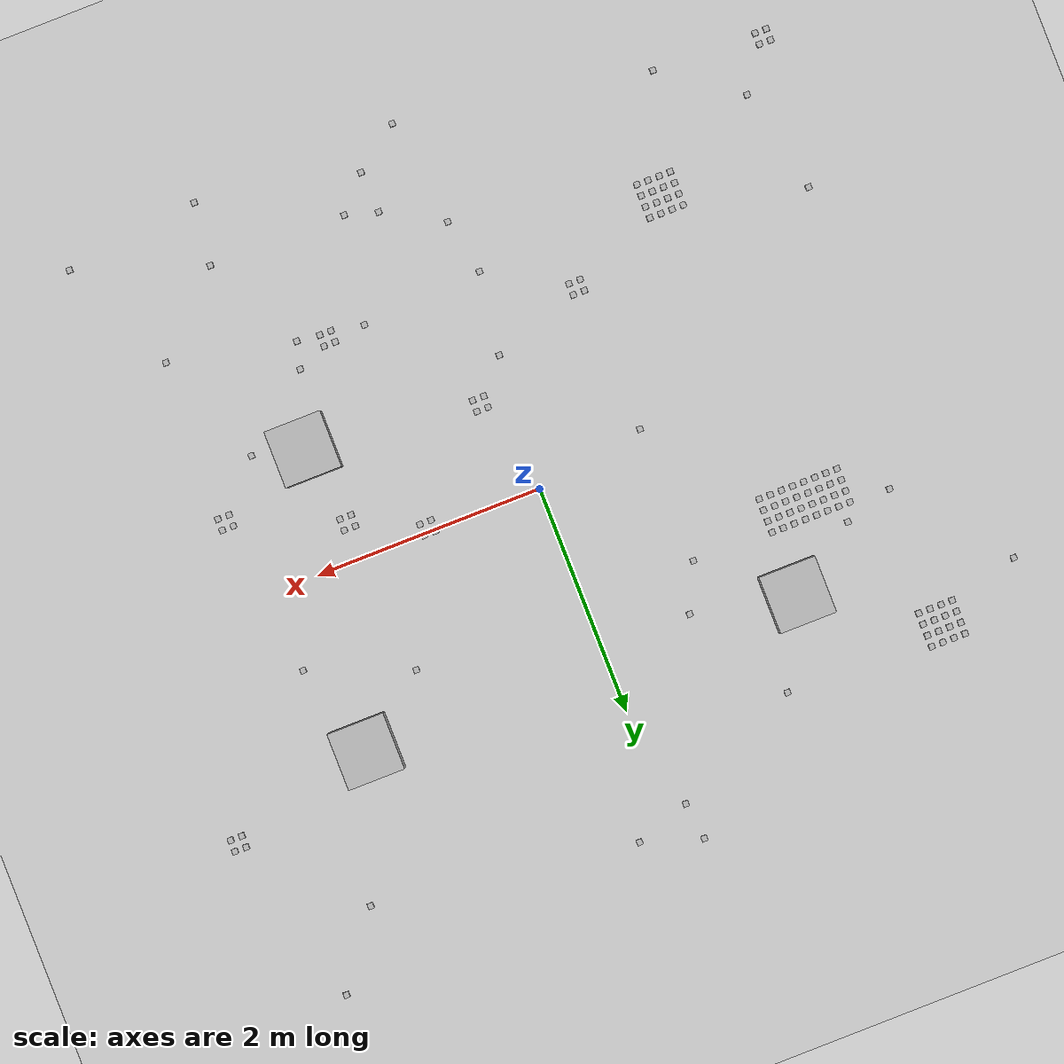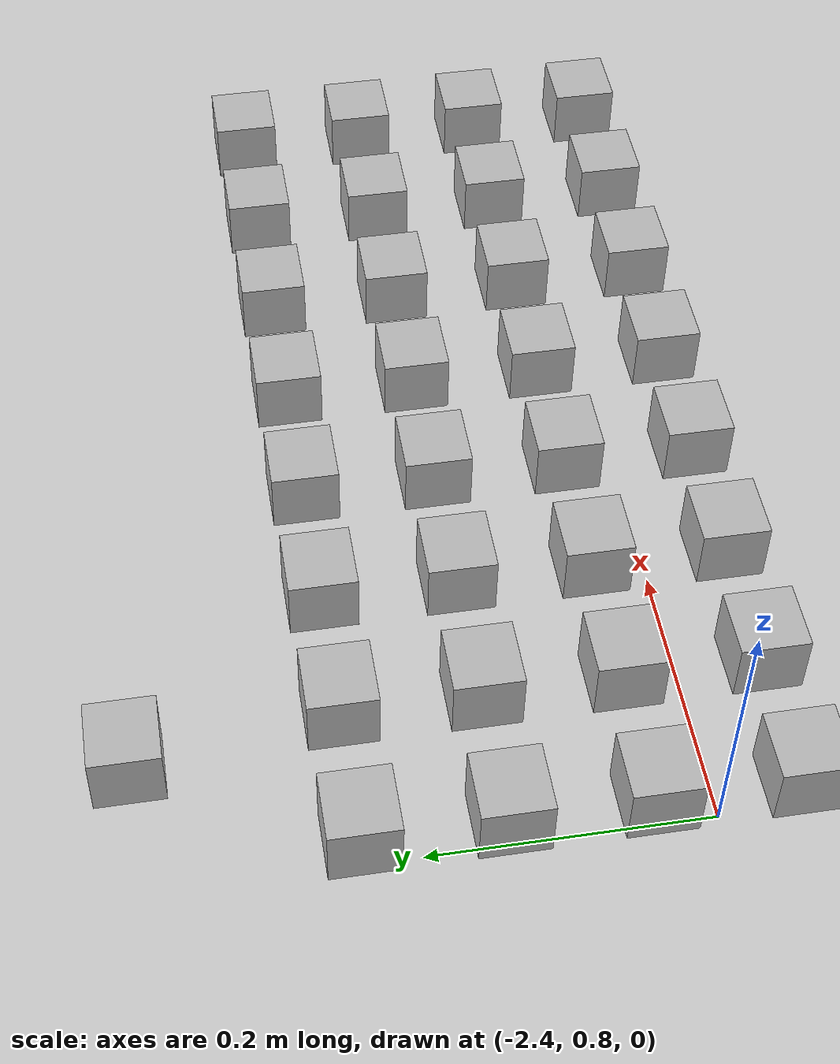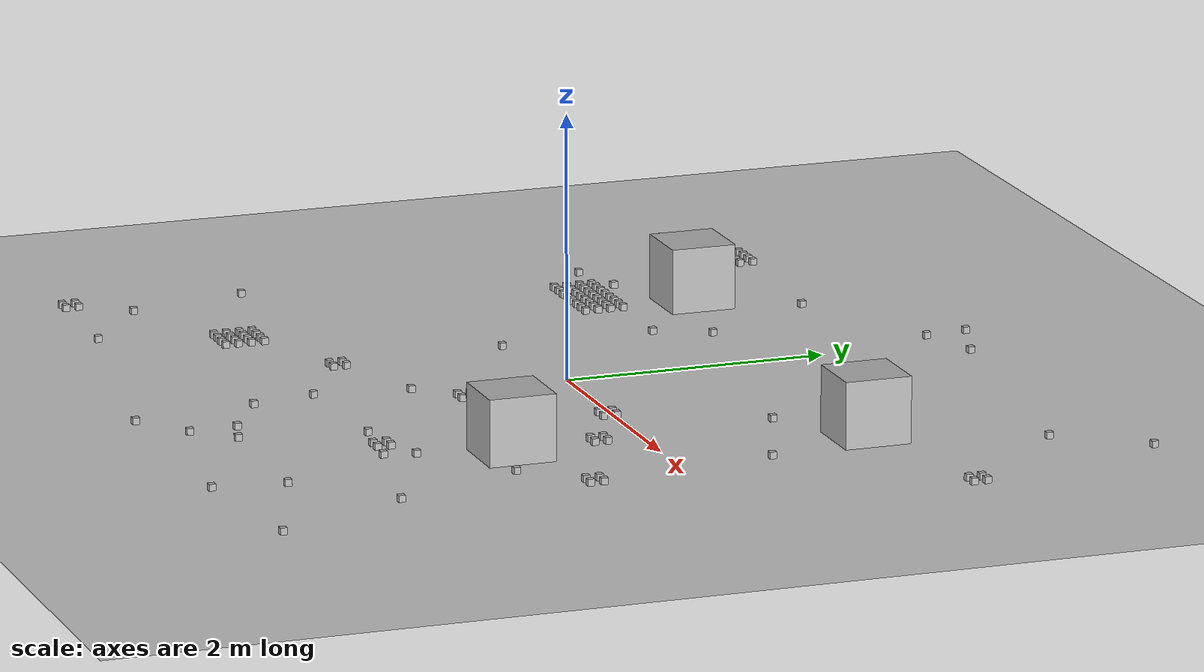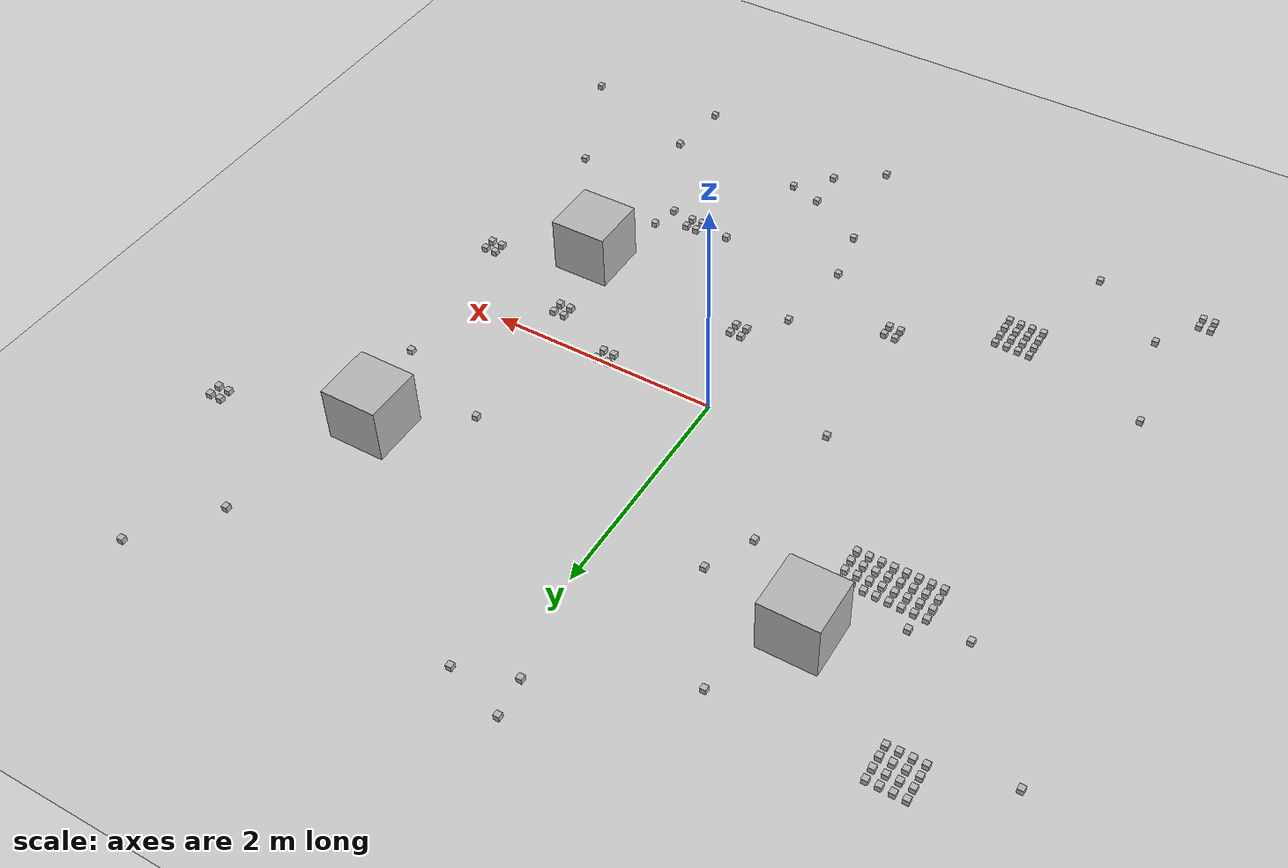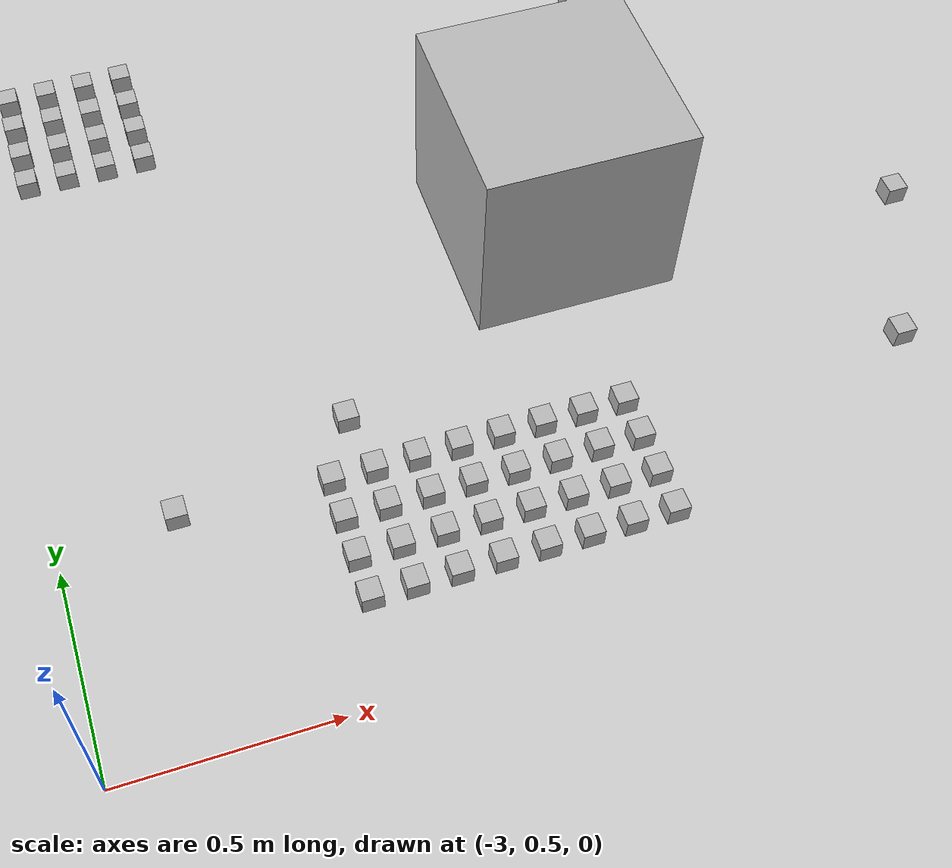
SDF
<sdf version="1.6">
 <world name="default">
  <model name="ground_plane">
   <static>1</static>
   <link name="link">
    <collision name="collision">
     <geometry><plane><normal>0 0 1</normal><size>100 100</size></plane></geometry>
     <surface><friction><ode><mu>100</mu><mu2>50</mu2></ode></friction></surface>
    </collision>
    <visual name="visual">
     <cast_shadows>0</cast_shadows>
     <geometry><plane><normal>0 0 1</normal><size>100 100</size></plane></geometry>
     <material>
      <script><uri>file://media/materials/scripts/gazebo.material</uri><name>Gazebo/Grey</name></script>
     </material>
    </visual>
   </link>
  </model>
  <light name="sun" type="directional">
   <pose>0 0 10 0 -0 0</pose>
   <diffuse>0.8 0.8 0.8 1</diffuse>
   <specular>0.1 0.1 0.1 1</specular>
   <attenuation>
    <range>1000</range>
    <constant>0.9</constant>
    <linear>0.01</linear>
    <quadratic>0.001</quadratic>
   </attenuation>
   <direction>-0.5 0.5 -1</direction>
  </light>
  <plugin name="SetupWorld" filename="libgazebo_plugins.so"/>
  <gravity>0 0 -9.8</gravity>
  <magnetic_field>6e-06 2.3e-05 -4.2e-05</magnetic_field>
  <atmosphere type="adiabatic"/>
  <physics name="default_physics" default="0" type="ode">
   <max_step_size>0.001</max_step_size>
   <real_time_factor>1</real_time_factor>
   <real_time_update_rate>1000</real_time_update_rate>
  </physics>
  <scene><ambient>0.4 0.4 0.4 1</ambient><background>0.7 0.7 0.7 1</background><shadows>1</shadows></scene>
  <spherical_coordinates>
   <surface_model>EARTH_WGS84</surface_model>
   <latitude_deg>0</latitude_deg>
   <longitude_deg>0</longitude_deg>
   <elevation>0</elevation>
   <heading_deg>0</heading_deg>
  </spherical_coordinates>
  <model name="at0">
   <static>0</static>
   <link name="link">
    <inertial>
     <mass>0.01</mass>
     <inertia><ixx>4e-05</ixx><ixy>0</ixy><ixz>0</ixz><iyy>4e-05</iyy><iyz>0</iyz><izz>4e-05</izz></inertia>
    </inertial>
    <visual name="visual">
     <geometry><box><size>0.05 0.05 0.05</size></box></geometry>
     <material>
      <script>
       <uri>model://at0/materials/scripts</uri>
       <uri>model://at0/materials/textures</uri>
       <name>at0/Diffuse</name>
      </script>
     </material>
    </visual>
    <collision name="collision">
     <geometry><box><size>0.05 0.05 0.05</size></box></geometry>
     <surface><friction><ode><mu>0.8</mu><mu2>0.7</mu2></ode></friction></surface>
    </collision>
   </link>
   <pose>-2.38131 0.73932 0.025 0 -0 0</pose>
  </model>
  <model name="at1">
   <static>0</static>
   <link name="link">
    <inertial>
     <mass>0.01</mass>
     <inertia><ixx>4e-05</ixx><ixy>0</ixy><ixz>0</ixz><iyy>4e-05</iyy><iyz>0</iyz><izz>4e-05</izz></inertia>
    </inertial>
    <visual name="visual">
     <geometry><box><size>0.05 0.05 0.05</size></box></geometry>
     <material>
      <script>
       <uri>model://at0/materials/scripts</uri>
       <uri>model://at0/materials/textures</uri>
       <name>at0/Diffuse</name>
      </script>
     </material>
    </visual>
    <collision name="collision">
     <geometry><box><size>0.05 0.05 0.05</size></box></geometry>
     <surface><friction><ode><mu>0.8</mu><mu2>0.7</mu2></ode></friction></surface>
    </collision>
   </link>
   <pose>-2.28131 0.73932 0.025 0 -0 0</pose>
  </model>
  <model name="at2">
   <static>0</static>
   <link name="link">
    <inertial>
     <mass>0.01</mass>
     <inertia><ixx>4e-05</ixx><ixy>0</ixy><ixz>0</ixz><iyy>4e-05</iyy><iyz>0</iyz><izz>4e-05</izz></inertia>
    </inertial>
    <visual name="visual">
     <geometry><box><size>0.05 0.05 0.05</size></box></geometry>
     <material>
      <script>
       <uri>model://at0/materials/scripts</uri>
       <uri>model://at0/materials/textures</uri>
       <name>at0/Diffuse</name>
      </script>
     </material>
    </visual>
    <collision name="collision">
     <geometry><box><size>0.05 0.05 0.05</size></box></geometry>
     <surface><friction><ode><mu>0.8</mu><mu2>0.7</mu2></ode></friction></surface>
    </collision>
   </link>
   <pose>-2.18131 0.73932 0.025 0 -0 0</pose>
  </model>
  <model name="at3">
   <static>0</static>
   <link name="link">
    <inertial>
     <mass>0.01</mass>
     <inertia><ixx>4e-05</ixx><ixy>0</ixy><ixz>0</ixz><iyy>4e-05</iyy><iyz>0</iyz><izz>4e-05</izz></inertia>
    </inertial>
    <visual name="visual">
     <geometry><box><size>0.05 0.05 0.05</size></box></geometry>
     <material>
      <script>
       <uri>model://at0/materials/scripts</uri>
       <uri>model://at0/materials/textures</uri>
       <name>at0/Diffuse</name>
      </script>
     </material>
    </visual>
    <collision name="collision">
     <geometry><box><size>0.05 0.05 0.05</size></box></geometry>
     <surface><friction><ode><mu>0.8</mu><mu2>0.7</mu2></ode></friction></surface>
    </collision>
   </link>
   <pose>-2.08131 0.73932 0.025 0 -0 0</pose>
  </model>
  <model name="at4">
   <static>0</static>
   <link name="link">
    <inertial>
     <mass>0.01</mass>
     <inertia><ixx>4e-05</ixx><ixy>0</ixy><ixz>0</ixz><iyy>4e-05</iyy><iyz>0</iyz><izz>4e-05</izz></inertia>
    </inertial>
    <visual name="visual">
     <geometry><box><size>0.05 0.05 0.05</size></box></geometry>
     <material>
      <script>
       <uri>model://at0/materials/scripts</uri>
       <uri>model://at0/materials/textures</uri>
       <name>at0/Diffuse</name>
      </script>
     </material>
    </visual>
    <collision name="collision">
     <geometry><box><size>0.05 0.05 0.05</size></box></geometry>
     <surface><friction><ode><mu>0.8</mu><mu2>0.7</mu2></ode></friction></surface>
    </collision>
   </link>
   <pose>-1.98131 0.73932 0.025 0 -0 0</pose>
  </model>
  <model name="at5">
   <static>0</static>
   <link name="link">
    <inertial>
     <mass>0.01</mass>
     <inertia><ixx>4e-05</ixx><ixy>0</ixy><ixz>0</ixz><iyy>4e-05</iyy><iyz>0</iyz><izz>4e-05</izz></inertia>
    </inertial>
    <visual name="visual">
     <geometry><box><size>0.05 0.05 0.05</size></box></geometry>
     <material>
      <script>
       <uri>model://at0/materials/scripts</uri>
       <uri>model://at0/materials/textures</uri>
       <name>at0/Diffuse</name>
      </script>
     </material>
    </visual>
    <collision name="collision">
     <geometry><box><size>0.05 0.05 0.05</size></box></geometry>
     <surface><friction><ode><mu>0.8</mu><mu2>0.7</mu2></ode></friction></surface>
    </collision>
   </link>
   <pose>-1.88131 0.73932 0.025 0 -0 0</pose>
  </model>
  <model name="at6">
   <static>0</static>
   <link name="link">
    <inertial>
     <mass>0.01</mass>
     <inertia><ixx>4e-05</ixx><ixy>0</ixy><ixz>0</ixz><iyy>4e-05</iyy><iyz>0</iyz><izz>4e-05</izz></inertia>
    </inertial>
    <visual name="visual">
     <geometry><box><size>0.05 0.05 0.05</size></box></geometry>
     <material>
      <script>
       <uri>model://at0/materials/scripts</uri>
       <uri>model://at0/materials/textures</uri>
       <name>at0/Diffuse</name>
      </script>
     </material>
    </visual>
    <collision name="collision">
     <geometry><box><size>0.05 0.05 0.05</size></box></geometry>
     <surface><friction><ode><mu>0.8</mu><mu2>0.7</mu2></ode></friction></surface>
    </collision>
   </link>
   <pose>-1.78131 0.73932 0.025 0 -0 0</pose>
  </model>
  <model name="at7">
   <static>0</static>
   <link name="link">
    <inertial>
     <mass>0.01</mass>
     <inertia><ixx>4e-05</ixx><ixy>0</ixy><ixz>0</ixz><iyy>4e-05</iyy><iyz>0</iyz><izz>4e-05</izz></inertia>
    </inertial>
    <visual name="visual">
     <geometry><box><size>0.05 0.05 0.05</size></box></geometry>
     <material>
      <script>
       <uri>model://at0/materials/scripts</uri>
       <uri>model://at0/materials/textures</uri>
       <name>at0/Diffuse</name>
      </script>
     </material>
    </visual>
    <collision name="collision">
     <geometry><box><size>0.05 0.05 0.05</size></box></geometry>
     <surface><friction><ode><mu>0.8</mu><mu2>0.7</mu2></ode></friction></surface>
    </collision>
   </link>
   <pose>-1.68131 0.73932 0.025 0 -0 0</pose>
  </model>
  <model name="at8">
   <static>0</static>
   <link name="link">
    <inertial>
     <mass>0.01</mass>
     <inertia><ixx>4e-05</ixx><ixy>0</ixy><ixz>0</ixz><iyy>4e-05</iyy><iyz>0</iyz><izz>4e-05</izz></inertia>
    </inertial>
    <visual name="visual">
     <geometry><box><size>0.05 0.05 0.05</size></box></geometry>
     <material>
      <script>
       <uri>model://at0/materials/scripts</uri>
       <uri>model://at0/materials/textures</uri>
       <name>at0/Diffuse</name>
      </script>
     </material>
    </visual>
    <collision name="collision">
     <geometry><box><size>0.05 0.05 0.05</size></box></geometry>
     <surface><friction><ode><mu>0.8</mu><mu2>0.7</mu2></ode></friction></surface>
    </collision>
   </link>
   <pose>-2.38131 0.83932 0.025 0 -0 0</pose>
  </model>
  <model name="at9">
   <static>0</static>
   <link name="link">
    <inertial>
     <mass>0.01</mass>
     <inertia><ixx>4e-05</ixx><ixy>0</ixy><ixz>0</ixz><iyy>4e-05</iyy><iyz>0</iyz><izz>4e-05</izz></inertia>
    </inertial>
    <visual name="visual">
     <geometry><box><size>0.05 0.05 0.05</size></box></geometry>
     <material>
      <script>
       <uri>model://at0/materials/scripts</uri>
       <uri>model://at0/materials/textures</uri>
       <name>at0/Diffuse</name>
      </script>
     </material>
    </visual>
    <collision name="collision">
     <geometry><box><size>0.05 0.05 0.05</size></box></geometry>
     <surface><friction><ode><mu>0.8</mu><mu2>0.7</mu2></ode></friction></surface>
    </collision>
   </link>
   <pose>-2.28131 0.83932 0.025 0 -0 0</pose>
  </model>
  <model name="at10">
   <static>0</static>
   <link name="link">
    <inertial>
     <mass>0.01</mass>
     <inertia><ixx>4e-05</ixx><ixy>0</ixy><ixz>0</ixz><iyy>4e-05</iyy><iyz>0</iyz><izz>4e-05</izz></inertia>
    </inertial>
    <visual name="visual">
     <geometry><box><size>0.05 0.05 0.05</size></box></geometry>
     <material>
      <script>
       <uri>model://at0/materials/scripts</uri>
       <uri>model://at0/materials/textures</uri>
       <name>at0/Diffuse</name>
      </script>
     </material>
    </visual>
    <collision name="collision">
     <geometry><box><size>0.05 0.05 0.05</size></box></geometry>
     <surface><friction><ode><mu>0.8</mu><mu2>0.7</mu2></ode></friction></surface>
    </collision>
   </link>
   <pose>-2.18131 0.83932 0.025 0 -0 0</pose>
  </model>
  <model name="at11">
   <static>0</static>
   <link name="link">
    <inertial>
     <mass>0.01</mass>
     <inertia><ixx>4e-05</ixx><ixy>0</ixy><ixz>0</ixz><iyy>4e-05</iyy><iyz>0</iyz><izz>4e-05</izz></inertia>
    </inertial>
    <visual name="visual">
     <geometry><box><size>0.05 0.05 0.05</size></box></geometry>
     <material>
      <script>
       <uri>model://at0/materials/scripts</uri>
       <uri>model://at0/materials/textures</uri>
       <name>at0/Diffuse</name>
      </script>
     </material>
    </visual>
    <collision name="collision">
     <geometry><box><size>0.05 0.05 0.05</size></box></geometry>
     <surface><friction><ode><mu>0.8</mu><mu2>0.7</mu2></ode></friction></surface>
    </collision>
   </link>
   <pose>-2.08131 0.83932 0.025 0 -0 0</pose>
  </model>
  <model name="at12">
   <static>0</static>
   <link name="link">
    <inertial>
     <mass>0.01</mass>
     <inertia><ixx>4e-05</ixx><ixy>0</ixy><ixz>0</ixz><iyy>4e-05</iyy><iyz>0</iyz><izz>4e-05</izz></inertia>
    </inertial>
    <visual name="visual">
     <geometry><box><size>0.05 0.05 0.05</size></box></geometry>
     <material>
      <script>
       <uri>model://at0/materials/scripts</uri>
       <uri>model://at0/materials/textures</uri>
       <name>at0/Diffuse</name>
      </script>
     </material>
    </visual>
    <collision name="collision">
     <geometry><box><size>0.05 0.05 0.05</size></box></geometry>
     <surface><friction><ode><mu>0.8</mu><mu2>0.7</mu2></ode></friction></surface>
    </collision>
   </link>
   <pose>-1.98131 0.83932 0.025 0 -0 0</pose>
  </model>
  <model name="at13">
   <static>0</static>
   <link name="link">
    <inertial>
     <mass>0.01</mass>
     <inertia><ixx>4e-05</ixx><ixy>0</ixy><ixz>0</ixz><iyy>4e-05</iyy><iyz>0</iyz><izz>4e-05</izz></inertia>
    </inertial>
    <visual name="visual">
     <geometry><box><size>0.05 0.05 0.05</size></box></geometry>
     <material>
      <script>
       <uri>model://at0/materials/scripts</uri>
       <uri>model://at0/materials/textures</uri>
       <name>at0/Diffuse</name>
      </script>
     </material>
    </visual>
    <collision name="collision">
     <geometry><box><size>0.05 0.05 0.05</size></box></geometry>
     <surface><friction><ode><mu>0.8</mu><mu2>0.7</mu2></ode></friction></surface>
    </collision>
   </link>
   <pose>-1.88131 0.83932 0.025 0 -0 0</pose>
  </model>
  <model name="at14">
   <static>0</static>
   <link name="link">
    <inertial>
     <mass>0.01</mass>
     <inertia><ixx>4e-05</ixx><ixy>0</ixy><ixz>0</ixz><iyy>4e-05</iyy><iyz>0</iyz><izz>4e-05</izz></inertia>
    </inertial>
    <visual name="visual">
     <geometry><box><size>0.05 0.05 0.05</size></box></geometry>
     <material>
      <script>
       <uri>model://at0/materials/scripts</uri>
       <uri>model://at0/materials/textures</uri>
       <name>at0/Diffuse</name>
      </script>
     </material>
    </visual>
    <collision name="collision">
     <geometry><box><size>0.05 0.05 0.05</size></box></geometry>
     <surface><friction><ode><mu>0.8</mu><mu2>0.7</mu2></ode></friction></surface>
    </collision>
   </link>
   <pose>-1.78131 0.83932 0.025 0 -0 0</pose>
  </model>
  <model name="at15">
   <static>0</static>
   <link name="link">
    <inertial>
     <mass>0.01</mass>
     <inertia><ixx>4e-05</ixx><ixy>0</ixy><ixz>0</ixz><iyy>4e-05</iyy><iyz>0</iyz><izz>4e-05</izz></inertia>
    </inertial>
    <visual name="visual">
     <geometry><box><size>0.05 0.05 0.05</size></box></geometry>
     <material>
      <script>
       <uri>model://at0/materials/scripts</uri>
       <uri>model://at0/materials/textures</uri>
       <name>at0/Diffuse</name>
      </script>
     </material>
    </visual>
    <collision name="collision">
     <geometry><box><size>0.05 0.05 0.05</size></box></geometry>
     <surface><friction><ode><mu>0.8</mu><mu2>0.7</mu2></ode></friction></surface>
    </collision>
   </link>
   <pose>-1.68131 0.83932 0.025 0 -0 0</pose>
  </model>
  <model name="at16">
   <static>0</static>
   <link name="link">
    <inertial>
     <mass>0.01</mass>
     <inertia><ixx>4e-05</ixx><ixy>0</ixy><ixz>0</ixz><iyy>4e-05</iyy><iyz>0</iyz><izz>4e-05</izz></inertia>
    </inertial>
    <visual name="visual">
     <geometry><box><size>0.05 0.05 0.05</size></box></geometry>
     <material>
      <script>
       <uri>model://at0/materials/scripts</uri>
       <uri>model://at0/materials/textures</uri>
       <name>at0/Diffuse</name>
      </script>
     </material>
    </visual>
    <collision name="collision">
     <geometry><box><size>0.05 0.05 0.05</size></box></geometry>
     <surface><friction><ode><mu>0.8</mu><mu2>0.7</mu2></ode></friction></surface>
    </collision>
   </link>
   <pose>-2.38131 0.93932 0.025 0 -0 0</pose>
  </model>
  <model name="at17">
   <static>0</static>
   <link name="link">
    <inertial>
     <mass>0.01</mass>
     <inertia><ixx>4e-05</ixx><ixy>0</ixy><ixz>0</ixz><iyy>4e-05</iyy><iyz>0</iyz><izz>4e-05</izz></inertia>
    </inertial>
    <visual name="visual">
     <geometry><box><size>0.05 0.05 0.05</size></box></geometry>
     <material>
      <script>
       <uri>model://at0/materials/scripts</uri>
       <uri>model://at0/materials/textures</uri>
       <name>at0/Diffuse</name>
      </script>
     </material>
    </visual>
    <collision name="collision">
     <geometry><box><size>0.05 0.05 0.05</size></box></geometry>
     <surface><friction><ode><mu>0.8</mu><mu2>0.7</mu2></ode></friction></surface>
    </collision>
   </link>
   <pose>-2.28131 0.93932 0.025 0 -0 0</pose>
  </model>
  <model name="at18">
   <static>0</static>
   <link name="link">
    <inertial>
     <mass>0.01</mass>
     <inertia><ixx>4e-05</ixx><ixy>0</ixy><ixz>0</ixz><iyy>4e-05</iyy><iyz>0</iyz><izz>4e-05</izz></inertia>
    </inertial>
    <visual name="visual">
     <geometry><box><size>0.05 0.05 0.05</size></box></geometry>
     <material>
      <script>
       <uri>model://at0/materials/scripts</uri>
       <uri>model://at0/materials/textures</uri>
       <name>at0/Diffuse</name>
      </script>
     </material>
    </visual>
    <collision name="collision">
     <geometry><box><size>0.05 0.05 0.05</size></box></geometry>
     <surface><friction><ode><mu>0.8</mu><mu2>0.7</mu2></ode></friction></surface>
    </collision>
   </link>
   <pose>-2.18131 0.93932 0.025 0 -0 0</pose>
  </model>
  <model name="at19">
   <static>0</static>
   <link name="link">
    <inertial>
     <mass>0.01</mass>
     <inertia><ixx>4e-05</ixx><ixy>0</ixy><ixz>0</ixz><iyy>4e-05</iyy><iyz>0</iyz><izz>4e-05</izz></inertia>
    </inertial>
    <visual name="visual">
     <geometry><box><size>0.05 0.05 0.05</size></box></geometry>
     <material>
      <script>
       <uri>model://at0/materials/scripts</uri>
       <uri>model://at0/materials/textures</uri>
       <name>at0/Diffuse</name>
      </script>
     </material>
    </visual>
    <collision name="collision">
     <geometry><box><size>0.05 0.05 0.05</size></box></geometry>
     <surface><friction><ode><mu>0.8</mu><mu2>0.7</mu2></ode></friction></surface>
    </collision>
   </link>
   <pose>-2.08131 0.93932 0.025 0 -0 0</pose>
  </model>
  <model name="at20">
   <static>0</static>
   <link name="link">
    <inertial>
     <mass>0.01</mass>
     <inertia><ixx>4e-05</ixx><ixy>0</ixy><ixz>0</ixz><iyy>4e-05</iyy><iyz>0</iyz><izz>4e-05</izz></inertia>
    </inertial>
    <visual name="visual">
     <geometry><box><size>0.05 0.05 0.05</size></box></geometry>
     <material>
      <script>
       <uri>model://at0/materials/scripts</uri>
       <uri>model://at0/materials/textures</uri>
       <name>at0/Diffuse</name>
      </script>
     </material>
    </visual>
    <collision name="collision">
     <geometry><box><size>0.05 0.05 0.05</size></box></geometry>
     <surface><friction><ode><mu>0.8</mu><mu2>0.7</mu2></ode></friction></surface>
    </collision>
   </link>
   <pose>-1.98131 0.93932 0.025 0 -0 0</pose>
  </model>
  <model name="at21">
   <static>0</static>
   <link name="link">
    <inertial>
     <mass>0.01</mass>
     <inertia><ixx>4e-05</ixx><ixy>0</ixy><ixz>0</ixz><iyy>4e-05</iyy><iyz>0</iyz><izz>4e-05</izz></inertia>
    </inertial>
    <visual name="visual">
     <geometry><box><size>0.05 0.05 0.05</size></box></geometry>
     <material>
      <script>
       <uri>model://at0/materials/scripts</uri>
       <uri>model://at0/materials/textures</uri>
       <name>at0/Diffuse</name>
      </script>
     </material>
    </visual>
    <collision name="collision">
     <geometry><box><size>0.05 0.05 0.05</size></box></geometry>
     <surface><friction><ode><mu>0.8</mu><mu2>0.7</mu2></ode></friction></surface>
    </collision>
   </link>
   <pose>-1.88131 0.93932 0.025 0 -0 0</pose>
  </model>
  <model name="at22">
   <static>0</static>
   <link name="link">
    <inertial>
     <mass>0.01</mass>
     <inertia><ixx>4e-05</ixx><ixy>0</ixy><ixz>0</ixz><iyy>4e-05</iyy><iyz>0</iyz><izz>4e-05</izz></inertia>
    </inertial>
    <visual name="visual">
     <geometry><box><size>0.05 0.05 0.05</size></box></geometry>
     <material>
      <script>
       <uri>model://at0/materials/scripts</uri>
       <uri>model://at0/materials/textures</uri>
       <name>at0/Diffuse</name>
      </script>
     </material>
    </visual>
    <collision name="collision">
     <geometry><box><size>0.05 0.05 0.05</size></box></geometry>
     <surface><friction><ode><mu>0.8</mu><mu2>0.7</mu2></ode></friction></surface>
    </collision>
   </link>
   <pose>-1.78131 0.93932 0.025 0 -0 0</pose>
  </model>
  <model name="at23">
   <static>0</static>
   <link name="link">
    <inertial>
     <mass>0.01</mass>
     <inertia><ixx>4e-05</ixx><ixy>0</ixy><ixz>0</ixz><iyy>4e-05</iyy><iyz>0</iyz><izz>4e-05</izz></inertia>
    </inertial>
    <visual name="visual">
     <geometry><box><size>0.05 0.05 0.05</size></box></geometry>
     <material>
      <script>
       <uri>model://at0/materials/scripts</uri>
       <uri>model://at0/materials/textures</uri>
       <name>at0/Diffuse</name>
      </script>
     </material>
    </visual>
    <collision name="collision">
     <geometry><box><size>0.05 0.05 0.05</size></box></geometry>
     <surface><friction><ode><mu>0.8</mu><mu2>0.7</mu2></ode></friction></surface>
    </collision>
   </link>
   <pose>-1.68131 0.93932 0.025 0 -0 0</pose>
  </model>
  <model name="at24">
   <static>0</static>
   <link name="link">
    <inertial>
     <mass>0.01</mass>
     <inertia><ixx>4e-05</ixx><ixy>0</ixy><ixz>0</ixz><iyy>4e-05</iyy><iyz>0</iyz><izz>4e-05</izz></inertia>
    </inertial>
    <visual name="visual">
     <geometry><box><size>0.05 0.05 0.05</size></box></geometry>
     <material>
      <script>
       <uri>model://at0/materials/scripts</uri>
       <uri>model://at0/materials/textures</uri>
       <name>at0/Diffuse</name>
      </script>
     </material>
    </visual>
    <collision name="collision">
     <geometry><box><size>0.05 0.05 0.05</size></box></geometry>
     <surface><friction><ode><mu>0.8</mu><mu2>0.7</mu2></ode></friction></surface>
    </collision>
   </link>
   <pose>-2.38131 1.03932 0.025 0 -0 0</pose>
  </model>
  <model name="at25">
   <static>0</static>
   <link name="link">
    <inertial>
     <mass>0.01</mass>
     <inertia><ixx>4e-05</ixx><ixy>0</ixy><ixz>0</ixz><iyy>4e-05</iyy><iyz>0</iyz><izz>4e-05</izz></inertia>
    </inertial>
    <visual name="visual">
     <geometry><box><size>0.05 0.05 0.05</size></box></geometry>
     <material>
      <script>
       <uri>model://at0/materials/scripts</uri>
       <uri>model://at0/materials/textures</uri>
       <name>at0/Diffuse</name>
      </script>
     </material>
    </visual>
    <collision name="collision">
     <geometry><box><size>0.05 0.05 0.05</size></box></geometry>
     <surface><friction><ode><mu>0.8</mu><mu2>0.7</mu2></ode></friction></surface>
    </collision>
   </link>
   <pose>-2.28131 1.03932 0.025 0 -0 0</pose>
  </model>
  <model name="at26">
   <static>0</static>
   <link name="link">
    <inertial>
     <mass>0.01</mass>
     <inertia><ixx>4e-05</ixx><ixy>0</ixy><ixz>0</ixz><iyy>4e-05</iyy><iyz>0</iyz><izz>4e-05</izz></inertia>
    </inertial>
    <visual name="visual">
     <geometry><box><size>0.05 0.05 0.05</size></box></geometry>
     <material>
      <script>
       <uri>model://at0/materials/scripts</uri>
       <uri>model://at0/materials/textures</uri>
       <name>at0/Diffuse</name>
      </script>
     </material>
    </visual>
    <collision name="collision">
     <geometry><box><size>0.05 0.05 0.05</size></box></geometry>
     <surface><friction><ode><mu>0.8</mu><mu2>0.7</mu2></ode></friction></surface>
    </collision>
   </link>
   <pose>-2.18131 1.03932 0.025 0 -0 0</pose>
  </model>
  <model name="at27">
   <static>0</static>
   <link name="link">
    <inertial>
     <mass>0.01</mass>
     <inertia><ixx>4e-05</ixx><ixy>0</ixy><ixz>0</ixz><iyy>4e-05</iyy><iyz>0</iyz><izz>4e-05</izz></inertia>
    </inertial>
    <visual name="visual">
     <geometry><box><size>0.05 0.05 0.05</size></box></geometry>
     <material>
      <script>
       <uri>model://at0/materials/scripts</uri>
       <uri>model://at0/materials/textures</uri>
       <name>at0/Diffuse</name>
      </script>
     </material>
    </visual>
    <collision name="collision">
     <geometry><box><size>0.05 0.05 0.05</size></box></geometry>
     <surface><friction><ode><mu>0.8</mu><mu2>0.7</mu2></ode></friction></surface>
    </collision>
   </link>
   <pose>-2.08131 1.03932 0.025 0 -0 0</pose>
  </model>
  <model name="at28">
   <static>0</static>
   <link name="link">
    <inertial>
     <mass>0.01</mass>
     <inertia><ixx>4e-05</ixx><ixy>0</ixy><ixz>0</ixz><iyy>4e-05</iyy><iyz>0</iyz><izz>4e-05</izz></inertia>
    </inertial>
    <visual name="visual">
     <geometry><box><size>0.05 0.05 0.05</size></box></geometry>
     <material>
      <script>
       <uri>model://at0/materials/scripts</uri>
       <uri>model://at0/materials/textures</uri>
       <name>at0/Diffuse</name>
      </script>
     </material>
    </visual>
    <collision name="collision">
     <geometry><box><size>0.05 0.05 0.05</size></box></geometry>
     <surface><friction><ode><mu>0.8</mu><mu2>0.7</mu2></ode></friction></surface>
    </collision>
   </link>
   <pose>-1.98131 1.03932 0.025 0 -0 0</pose>
  </model>
  <model name="at29">
   <static>0</static>
   <link name="link">
    <inertial>
     <mass>0.01</mass>
     <inertia><ixx>4e-05</ixx><ixy>0</ixy><ixz>0</ixz><iyy>4e-05</iyy><iyz>0</iyz><izz>4e-05</izz></inertia>
    </inertial>
    <visual name="visual">
     <geometry><box><size>0.05 0.05 0.05</size></box></geometry>
     <material>
      <script>
       <uri>model://at0/materials/scripts</uri>
       <uri>model://at0/materials/textures</uri>
       <name>at0/Diffuse</name>
      </script>
     </material>
    </visual>
    <collision name="collision">
     <geometry><box><size>0.05 0.05 0.05</size></box></geometry>
     <surface><friction><ode><mu>0.8</mu><mu2>0.7</mu2></ode></friction></surface>
    </collision>
   </link>
   <pose>-1.88131 1.03932 0.025 0 -0 0</pose>
  </model>
  <model name="at30">
   <static>0</static>
   <link name="link">
    <inertial>
     <mass>0.01</mass>
     <inertia><ixx>4e-05</ixx><ixy>0</ixy><ixz>0</ixz><iyy>4e-05</iyy><iyz>0</iyz><izz>4e-05</izz></inertia>
    </inertial>
    <visual name="visual">
     <geometry><box><size>0.05 0.05 0.05</size></box></geometry>
     <material>
      <script>
       <uri>model://at0/materials/scripts</uri>
       <uri>model://at0/materials/textures</uri>
       <name>at0/Diffuse</name>
      </script>
     </material>
    </visual>
    <collision name="collision">
     <geometry><box><size>0.05 0.05 0.05</size></box></geometry>
     <surface><friction><ode><mu>0.8</mu><mu2>0.7</mu2></ode></friction></surface>
    </collision>
   </link>
   <pose>-1.78131 1.03932 0.025 0 -0 0</pose>
  </model>
  <model name="at31">
   <static>0</static>
   <link name="link">
    <inertial>
     <mass>0.01</mass>
     <inertia><ixx>4e-05</ixx><ixy>0</ixy><ixz>0</ixz><iyy>4e-05</iyy><iyz>0</iyz><izz>4e-05</izz></inertia>
    </inertial>
    <visual name="visual">
     <geometry><box><size>0.05 0.05 0.05</size></box></geometry>
     <material>
      <script>
       <uri>model://at0/materials/scripts</uri>
       <uri>model://at0/materials/textures</uri>
       <name>at0/Diffuse</name>
      </script>
     </material>
    </visual>
    <collision name="collision">
     <geometry><box><size>0.05 0.05 0.05</size></box></geometry>
     <surface><friction><ode><mu>0.8</mu><mu2>0.7</mu2></ode></friction></surface>
    </collision>
   </link>
   <pose>-1.68131 1.03932 0.025 0 -0 0</pose>
  </model>
  <model name="at32">
   <static>0</static>
   <link name="link">
    <inertial>
     <mass>0.01</mass>
     <inertia><ixx>4e-05</ixx><ixy>0</ixy><ixz>0</ixz><iyy>4e-05</iyy><iyz>0</iyz><izz>4e-05</izz></inertia>
    </inertial>
    <visual name="visual">
     <geometry><box><size>0.05 0.05 0.05</size></box></geometry>
     <material>
      <script>
       <uri>model://at0/materials/scripts</uri>
       <uri>model://at0/materials/textures</uri>
       <name>at0/Diffuse</name>
      </script>
     </material>
    </visual>
    <collision name="collision">
     <geometry><box><size>0.05 0.05 0.05</size></box></geometry>
     <surface><friction><ode><mu>0.8</mu><mu2>0.7</mu2></ode></friction></surface>
    </collision>
   </link>
   <pose>-1.98169 -2.08908 0.025 0 -0 0</pose>
  </model>
  <model name="at33">
   <static>0</static>
   <link name="link">
    <inertial>
     <mass>0.01</mass>
     <inertia><ixx>4e-05</ixx><ixy>0</ixy><ixz>0</ixz><iyy>4e-05</iyy><iyz>0</iyz><izz>4e-05</izz></inertia>
    </inertial>
    <visual name="visual">
     <geometry><box><size>0.05 0.05 0.05</size></box></geometry>
     <material>
      <script>
       <uri>model://at0/materials/scripts</uri>
       <uri>model://at0/materials/textures</uri>
       <name>at0/Diffuse</name>
      </script>
     </material>
    </visual>
    <collision name="collision">
     <geometry><box><size>0.05 0.05 0.05</size></box></geometry>
     <surface><friction><ode><mu>0.8</mu><mu2>0.7</mu2></ode></friction></surface>
    </collision>
   </link>
   <pose>-1.88169 -2.08908 0.025 0 -0 0</pose>
  </model>
  <model name="at34">
   <static>0</static>
   <link name="link">
    <inertial>
     <mass>0.01</mass>
     <inertia><ixx>4e-05</ixx><ixy>0</ixy><ixz>0</ixz><iyy>4e-05</iyy><iyz>0</iyz><izz>4e-05</izz></inertia>
    </inertial>
    <visual name="visual">
     <geometry><box><size>0.05 0.05 0.05</size></box></geometry>
     <material>
      <script>
       <uri>model://at0/materials/scripts</uri>
       <uri>model://at0/materials/textures</uri>
       <name>at0/Diffuse</name>
      </script>
     </material>
    </visual>
    <collision name="collision">
     <geometry><box><size>0.05 0.05 0.05</size></box></geometry>
     <surface><friction><ode><mu>0.8</mu><mu2>0.7</mu2></ode></friction></surface>
    </collision>
   </link>
   <pose>-1.78169 -2.08908 0.025 0 -0 0</pose>
  </model>
  <model name="at35">
   <static>0</static>
   <link name="link">
    <inertial>
     <mass>0.01</mass>
     <inertia><ixx>4e-05</ixx><ixy>0</ixy><ixz>0</ixz><iyy>4e-05</iyy><iyz>0</iyz><izz>4e-05</izz></inertia>
    </inertial>
    <visual name="visual">
     <geometry><box><size>0.05 0.05 0.05</size></box></geometry>
     <material>
      <script>
       <uri>model://at0/materials/scripts</uri>
       <uri>model://at0/materials/textures</uri>
       <name>at0/Diffuse</name>
      </script>
     </material>
    </visual>
    <collision name="collision">
     <geometry><box><size>0.05 0.05 0.05</size></box></geometry>
     <surface><friction><ode><mu>0.8</mu><mu2>0.7</mu2></ode></friction></surface>
    </collision>
   </link>
   <pose>-1.68169 -2.08908 0.025 0 -0 0</pose>
  </model>
  <model name="at36">
   <static>0</static>
   <link name="link">
    <inertial>
     <mass>0.01</mass>
     <inertia><ixx>4e-05</ixx><ixy>0</ixy><ixz>0</ixz><iyy>4e-05</iyy><iyz>0</iyz><izz>4e-05</izz></inertia>
    </inertial>
    <visual name="visual">
     <geometry><box><size>0.05 0.05 0.05</size></box></geometry>
     <material>
      <script>
       <uri>model://at0/materials/scripts</uri>
       <uri>model://at0/materials/textures</uri>
       <name>at0/Diffuse</name>
      </script>
     </material>
    </visual>
    <collision name="collision">
     <geometry><box><size>0.05 0.05 0.05</size></box></geometry>
     <surface><friction><ode><mu>0.8</mu><mu2>0.7</mu2></ode></friction></surface>
    </collision>
   </link>
   <pose>-1.98169 -1.98908 0.025 0 -0 0</pose>
  </model>
  <model name="at37">
   <static>0</static>
   <link name="link">
    <inertial>
     <mass>0.01</mass>
     <inertia><ixx>4e-05</ixx><ixy>0</ixy><ixz>0</ixz><iyy>4e-05</iyy><iyz>0</iyz><izz>4e-05</izz></inertia>
    </inertial>
    <visual name="visual">
     <geometry><box><size>0.05 0.05 0.05</size></box></geometry>
     <material>
      <script>
       <uri>model://at0/materials/scripts</uri>
       <uri>model://at0/materials/textures</uri>
       <name>at0/Diffuse</name>
      </script>
     </material>
    </visual>
    <collision name="collision">
     <geometry><box><size>0.05 0.05 0.05</size></box></geometry>
     <surface><friction><ode><mu>0.8</mu><mu2>0.7</mu2></ode></friction></surface>
    </collision>
   </link>
   <pose>-1.88169 -1.98908 0.025 0 -0 0</pose>
  </model>
  <model name="at38">
   <static>0</static>
   <link name="link">
    <inertial>
     <mass>0.01</mass>
     <inertia><ixx>4e-05</ixx><ixy>0</ixy><ixz>0</ixz><iyy>4e-05</iyy><iyz>0</iyz><izz>4e-05</izz></inertia>
    </inertial>
    <visual name="visual">
     <geometry><box><size>0.05 0.05 0.05</size></box></geometry>
     <material>
      <script>
       <uri>model://at0/materials/scripts</uri>
       <uri>model://at0/materials/textures</uri>
       <name>at0/Diffuse</name>
      </script>
     </material>
    </visual>
    <collision name="collision">
     <geometry><box><size>0.05 0.05 0.05</size></box></geometry>
     <surface><friction><ode><mu>0.8</mu><mu2>0.7</mu2></ode></friction></surface>
    </collision>
   </link>
   <pose>-1.78169 -1.98908 0.025 0 -0 0</pose>
  </model>
  <model name="at39">
   <static>0</static>
   <link name="link">
    <inertial>
     <mass>0.01</mass>
     <inertia><ixx>4e-05</ixx><ixy>0</ixy><ixz>0</ixz><iyy>4e-05</iyy><iyz>0</iyz><izz>4e-05</izz></inertia>
    </inertial>
    <visual name="visual">
     <geometry><box><size>0.05 0.05 0.05</size></box></geometry>
     <material>
      <script>
       <uri>model://at0/materials/scripts</uri>
       <uri>model://at0/materials/textures</uri>
       <name>at0/Diffuse</name>
      </script>
     </material>
    </visual>
    <collision name="collision">
     <geometry><box><size>0.05 0.05 0.05</size></box></geometry>
     <surface><friction><ode><mu>0.8</mu><mu2>0.7</mu2></ode></friction></surface>
    </collision>
   </link>
   <pose>-1.68169 -1.98908 0.025 0 -0 0</pose>
  </model>
  <model name="at40">
   <static>0</static>
   <link name="link">
    <inertial>
     <mass>0.01</mass>
     <inertia><ixx>4e-05</ixx><ixy>0</ixy><ixz>0</ixz><iyy>4e-05</iyy><iyz>0</iyz><izz>4e-05</izz></inertia>
    </inertial>
    <visual name="visual">
     <geometry><box><size>0.05 0.05 0.05</size></box></geometry>
     <material>
      <script>
       <uri>model://at0/materials/scripts</uri>
       <uri>model://at0/materials/textures</uri>
       <name>at0/Diffuse</name>
      </script>
     </material>
    </visual>
    <collision name="collision">
     <geometry><box><size>0.05 0.05 0.05</size></box></geometry>
     <surface><friction><ode><mu>0.8</mu><mu2>0.7</mu2></ode></friction></surface>
    </collision>
   </link>
   <pose>-1.98169 -1.88908 0.025 0 -0 0</pose>
  </model>
  <model name="at41">
   <static>0</static>
   <link name="link">
    <inertial>
     <mass>0.01</mass>
     <inertia><ixx>4e-05</ixx><ixy>0</ixy><ixz>0</ixz><iyy>4e-05</iyy><iyz>0</iyz><izz>4e-05</izz></inertia>
    </inertial>
    <visual name="visual">
     <geometry><box><size>0.05 0.05 0.05</size></box></geometry>
     <material>
      <script>
       <uri>model://at0/materials/scripts</uri>
       <uri>model://at0/materials/textures</uri>
       <name>at0/Diffuse</name>
      </script>
     </material>
    </visual>
    <collision name="collision">
     <geometry><box><size>0.05 0.05 0.05</size></box></geometry>
     <surface><friction><ode><mu>0.8</mu><mu2>0.7</mu2></ode></friction></surface>
    </collision>
   </link>
   <pose>-1.88169 -1.88908 0.025 0 -0 0</pose>
  </model>
  <model name="at42">
   <static>0</static>
   <link name="link">
    <inertial>
     <mass>0.01</mass>
     <inertia><ixx>4e-05</ixx><ixy>0</ixy><ixz>0</ixz><iyy>4e-05</iyy><iyz>0</iyz><izz>4e-05</izz></inertia>
    </inertial>
    <visual name="visual">
     <geometry><box><size>0.05 0.05 0.05</size></box></geometry>
     <material>
      <script>
       <uri>model://at0/materials/scripts</uri>
       <uri>model://at0/materials/textures</uri>
       <name>at0/Diffuse</name>
      </script>
     </material>
    </visual>
    <collision name="collision">
     <geometry><box><size>0.05 0.05 0.05</size></box></geometry>
     <surface><friction><ode><mu>0.8</mu><mu2>0.7</mu2></ode></friction></surface>
    </collision>
   </link>
   <pose>-1.78169 -1.88908 0.025 0 -0 0</pose>
  </model>
  <model name="at43">
   <static>0</static>
   <link name="link">
    <inertial>
     <mass>0.01</mass>
     <inertia><ixx>4e-05</ixx><ixy>0</ixy><ixz>0</ixz><iyy>4e-05</iyy><iyz>0</iyz><izz>4e-05</izz></inertia>
    </inertial>
    <visual name="visual">
     <geometry><box><size>0.05 0.05 0.05</size></box></geometry>
     <material>
      <script>
       <uri>model://at0/materials/scripts</uri>
       <uri>model://at0/materials/textures</uri>
       <name>at0/Diffuse</name>
      </script>
     </material>
    </visual>
    <collision name="collision">
     <geometry><box><size>0.05 0.05 0.05</size></box></geometry>
     <surface><friction><ode><mu>0.8</mu><mu2>0.7</mu2></ode></friction></surface>
    </collision>
   </link>
   <pose>-1.68169 -1.88908 0.025 0 -0 0</pose>
  </model>
  <model name="at44">
   <static>0</static>
   <link name="link">
    <inertial>
     <mass>0.01</mass>
     <inertia><ixx>4e-05</ixx><ixy>0</ixy><ixz>0</ixz><iyy>4e-05</iyy><iyz>0</iyz><izz>4e-05</izz></inertia>
    </inertial>
    <visual name="visual">
     <geometry><box><size>0.05 0.05 0.05</size></box></geometry>
     <material>
      <script>
       <uri>model://at0/materials/scripts</uri>
       <uri>model://at0/materials/textures</uri>
       <name>at0/Diffuse</name>
      </script>
     </material>
    </visual>
    <collision name="collision">
     <geometry><box><size>0.05 0.05 0.05</size></box></geometry>
     <surface><friction><ode><mu>0.8</mu><mu2>0.7</mu2></ode></friction></surface>
    </collision>
   </link>
   <pose>-1.98169 -1.78908 0.025 0 -0 0</pose>
  </model>
  <model name="at45">
   <static>0</static>
   <link name="link">
    <inertial>
     <mass>0.01</mass>
     <inertia><ixx>4e-05</ixx><ixy>0</ixy><ixz>0</ixz><iyy>4e-05</iyy><iyz>0</iyz><izz>4e-05</izz></inertia>
    </inertial>
    <visual name="visual">
     <geometry><box><size>0.05 0.05 0.05</size></box></geometry>
     <material>
      <script>
       <uri>model://at0/materials/scripts</uri>
       <uri>model://at0/materials/textures</uri>
       <name>at0/Diffuse</name>
      </script>
     </material>
    </visual>
    <collision name="collision">
     <geometry><box><size>0.05 0.05 0.05</size></box></geometry>
     <surface><friction><ode><mu>0.8</mu><mu2>0.7</mu2></ode></friction></surface>
    </collision>
   </link>
   <pose>-1.88169 -1.78908 0.025 0 -0 0</pose>
  </model>
  <model name="at46">
   <static>0</static>
   <link name="link">
    <inertial>
     <mass>0.01</mass>
     <inertia><ixx>4e-05</ixx><ixy>0</ixy><ixz>0</ixz><iyy>4e-05</iyy><iyz>0</iyz><izz>4e-05</izz></inertia>
    </inertial>
    <visual name="visual">
     <geometry><box><size>0.05 0.05 0.05</size></box></geometry>
     <material>
      <script>
       <uri>model://at0/materials/scripts</uri>
       <uri>model://at0/materials/textures</uri>
       <name>at0/Diffuse</name>
      </script>
     </material>
    </visual>
    <collision name="collision">
     <geometry><box><size>0.05 0.05 0.05</size></box></geometry>
     <surface><friction><ode><mu>0.8</mu><mu2>0.7</mu2></ode></friction></surface>
    </collision>
   </link>
   <pose>-1.78169 -1.78908 0.025 0 -0 0</pose>
  </model>
  <model name="at47">
   <static>0</static>
   <link name="link">
    <inertial>
     <mass>0.01</mass>
     <inertia><ixx>4e-05</ixx><ixy>0</ixy><ixz>0</ixz><iyy>4e-05</iyy><iyz>0</iyz><izz>4e-05</izz></inertia>
    </inertial>
    <visual name="visual">
     <geometry><box><size>0.05 0.05 0.05</size></box></geometry>
     <material>
      <script>
       <uri>model://at0/materials/scripts</uri>
       <uri>model://at0/materials/textures</uri>
       <name>at0/Diffuse</name>
      </script>
     </material>
    </visual>
    <collision name="collision">
     <geometry><box><size>0.05 0.05 0.05</size></box></geometry>
     <surface><friction><ode><mu>0.8</mu><mu2>0.7</mu2></ode></friction></surface>
    </collision>
   </link>
   <pose>-1.68169 -1.78908 0.025 0 -0 0</pose>
  </model>
  <model name="at48">
   <static>0</static>
   <link name="link">
    <inertial>
     <mass>0.01</mass>
     <inertia><ixx>4e-05</ixx><ixy>0</ixy><ixz>0</ixz><iyy>4e-05</iyy><iyz>0</iyz><izz>4e-05</izz></inertia>
    </inertial>
    <visual name="visual">
     <geometry><box><size>0.05 0.05 0.05</size></box></geometry>
     <material>
      <script>
       <uri>model://at0/materials/scripts</uri>
       <uri>model://at0/materials/textures</uri>
       <name>at0/Diffuse</name>
      </script>
     </material>
    </visual>
    <collision name="collision">
     <geometry><box><size>0.05 0.05 0.05</size></box></geometry>
     <surface><friction><ode><mu>0.8</mu><mu2>0.7</mu2></ode></friction></surface>
    </collision>
   </link>
   <pose>-2.88153 2.11714 0.025 0 -0 0</pose>
  </model>
  <model name="at49">
   <static>0</static>
   <link name="link">
    <inertial>
     <mass>0.01</mass>
     <inertia><ixx>4e-05</ixx><ixy>0</ixy><ixz>0</ixz><iyy>4e-05</iyy><iyz>0</iyz><izz>4e-05</izz></inertia>
    </inertial>
    <visual name="visual">
     <geometry><box><size>0.05 0.05 0.05</size></box></geometry>
     <material>
      <script>
       <uri>model://at0/materials/scripts</uri>
       <uri>model://at0/materials/textures</uri>
       <name>at0/Diffuse</name>
      </script>
     </material>
    </visual>
    <collision name="collision">
     <geometry><box><size>0.05 0.05 0.05</size></box></geometry>
     <surface><friction><ode><mu>0.8</mu><mu2>0.7</mu2></ode></friction></surface>
    </collision>
   </link>
   <pose>-2.78153 2.11714 0.025 0 -0 0</pose>
  </model>
  <model name="at50">
   <static>0</static>
   <link name="link">
    <inertial>
     <mass>0.01</mass>
     <inertia><ixx>4e-05</ixx><ixy>0</ixy><ixz>0</ixz><iyy>4e-05</iyy><iyz>0</iyz><izz>4e-05</izz></inertia>
    </inertial>
    <visual name="visual">
     <geometry><box><size>0.05 0.05 0.05</size></box></geometry>
     <material>
      <script>
       <uri>model://at0/materials/scripts</uri>
       <uri>model://at0/materials/textures</uri>
       <name>at0/Diffuse</name>
      </script>
     </material>
    </visual>
    <collision name="collision">
     <geometry><box><size>0.05 0.05 0.05</size></box></geometry>
     <surface><friction><ode><mu>0.8</mu><mu2>0.7</mu2></ode></friction></surface>
    </collision>
   </link>
   <pose>-2.68153 2.11714 0.025 0 -0 0</pose>
  </model>
  <model name="at51">
   <static>0</static>
   <link name="link">
    <inertial>
     <mass>0.01</mass>
     <inertia><ixx>4e-05</ixx><ixy>0</ixy><ixz>0</ixz><iyy>4e-05</iyy><iyz>0</iyz><izz>4e-05</izz></inertia>
    </inertial>
    <visual name="visual">
     <geometry><box><size>0.05 0.05 0.05</size></box></geometry>
     <material>
      <script>
       <uri>model://at0/materials/scripts</uri>
       <uri>model://at0/materials/textures</uri>
       <name>at0/Diffuse</name>
      </script>
     </material>
    </visual>
    <collision name="collision">
     <geometry><box><size>0.05 0.05 0.05</size></box></geometry>
     <surface><friction><ode><mu>0.8</mu><mu2>0.7</mu2></ode></friction></surface>
    </collision>
   </link>
   <pose>-2.58153 2.11714 0.025 0 -0 0</pose>
  </model>
  <model name="at52">
   <static>0</static>
   <link name="link">
    <inertial>
     <mass>0.01</mass>
     <inertia><ixx>4e-05</ixx><ixy>0</ixy><ixz>0</ixz><iyy>4e-05</iyy><iyz>0</iyz><izz>4e-05</izz></inertia>
    </inertial>
    <visual name="visual">
     <geometry><box><size>0.05 0.05 0.05</size></box></geometry>
     <material>
      <script>
       <uri>model://at0/materials/scripts</uri>
       <uri>model://at0/materials/textures</uri>
       <name>at0/Diffuse</name>
      </script>
     </material>
    </visual>
    <collision name="collision">
     <geometry><box><size>0.05 0.05 0.05</size></box></geometry>
     <surface><friction><ode><mu>0.8</mu><mu2>0.7</mu2></ode></friction></surface>
    </collision>
   </link>
   <pose>-2.88153 2.21714 0.025 0 -0 0</pose>
  </model>
  <model name="at53">
   <static>0</static>
   <link name="link">
    <inertial>
     <mass>0.01</mass>
     <inertia><ixx>4e-05</ixx><ixy>0</ixy><ixz>0</ixz><iyy>4e-05</iyy><iyz>0</iyz><izz>4e-05</izz></inertia>
    </inertial>
    <visual name="visual">
     <geometry><box><size>0.05 0.05 0.05</size></box></geometry>
     <material>
      <script>
       <uri>model://at0/materials/scripts</uri>
       <uri>model://at0/materials/textures</uri>
       <name>at0/Diffuse</name>
      </script>
     </material>
    </visual>
    <collision name="collision">
     <geometry><box><size>0.05 0.05 0.05</size></box></geometry>
     <surface><friction><ode><mu>0.8</mu><mu2>0.7</mu2></ode></friction></surface>
    </collision>
   </link>
   <pose>-2.78153 2.21714 0.025 0 -0 0</pose>
  </model>
  <model name="at54">
   <static>0</static>
   <link name="link">
    <inertial>
     <mass>0.01</mass>
     <inertia><ixx>4e-05</ixx><ixy>0</ixy><ixz>0</ixz><iyy>4e-05</iyy><iyz>0</iyz><izz>4e-05</izz></inertia>
    </inertial>
    <visual name="visual">
     <geometry><box><size>0.05 0.05 0.05</size></box></geometry>
     <material>
      <script>
       <uri>model://at0/materials/scripts</uri>
       <uri>model://at0/materials/textures</uri>
       <name>at0/Diffuse</name>
      </script>
     </material>
    </visual>
    <collision name="collision">
     <geometry><box><size>0.05 0.05 0.05</size></box></geometry>
     <surface><friction><ode><mu>0.8</mu><mu2>0.7</mu2></ode></friction></surface>
    </collision>
   </link>
   <pose>-2.68153 2.21714 0.025 0 -0 0</pose>
  </model>
  <model name="at55">
   <static>0</static>
   <link name="link">
    <inertial>
     <mass>0.01</mass>
     <inertia><ixx>4e-05</ixx><ixy>0</ixy><ixz>0</ixz><iyy>4e-05</iyy><iyz>0</iyz><izz>4e-05</izz></inertia>
    </inertial>
    <visual name="visual">
     <geometry><box><size>0.05 0.05 0.05</size></box></geometry>
     <material>
      <script>
       <uri>model://at0/materials/scripts</uri>
       <uri>model://at0/materials/textures</uri>
       <name>at0/Diffuse</name>
      </script>
     </material>
    </visual>
    <collision name="collision">
     <geometry><box><size>0.05 0.05 0.05</size></box></geometry>
     <surface><friction><ode><mu>0.8</mu><mu2>0.7</mu2></ode></friction></surface>
    </collision>
   </link>
   <pose>-2.58153 2.21714 0.025 0 -0 0</pose>
  </model>
  <model name="at56">
   <static>0</static>
   <link name="link">
    <inertial>
     <mass>0.01</mass>
     <inertia><ixx>4e-05</ixx><ixy>0</ixy><ixz>0</ixz><iyy>4e-05</iyy><iyz>0</iyz><izz>4e-05</izz></inertia>
    </inertial>
    <visual name="visual">
     <geometry><box><size>0.05 0.05 0.05</size></box></geometry>
     <material>
      <script>
       <uri>model://at0/materials/scripts</uri>
       <uri>model://at0/materials/textures</uri>
       <name>at0/Diffuse</name>
      </script>
     </material>
    </visual>
    <collision name="collision">
     <geometry><box><size>0.05 0.05 0.05</size></box></geometry>
     <surface><friction><ode><mu>0.8</mu><mu2>0.7</mu2></ode></friction></surface>
    </collision>
   </link>
   <pose>-2.88153 2.31714 0.025 0 -0 0</pose>
  </model>
  <model name="at57">
   <static>0</static>
   <link name="link">
    <inertial>
     <mass>0.01</mass>
     <inertia><ixx>4e-05</ixx><ixy>0</ixy><ixz>0</ixz><iyy>4e-05</iyy><iyz>0</iyz><izz>4e-05</izz></inertia>
    </inertial>
    <visual name="visual">
     <geometry><box><size>0.05 0.05 0.05</size></box></geometry>
     <material>
      <script>
       <uri>model://at0/materials/scripts</uri>
       <uri>model://at0/materials/textures</uri>
       <name>at0/Diffuse</name>
      </script>
     </material>
    </visual>
    <collision name="collision">
     <geometry><box><size>0.05 0.05 0.05</size></box></geometry>
     <surface><friction><ode><mu>0.8</mu><mu2>0.7</mu2></ode></friction></surface>
    </collision>
   </link>
   <pose>-2.78153 2.31714 0.025 0 -0 0</pose>
  </model>
  <model name="at58">
   <static>0</static>
   <link name="link">
    <inertial>
     <mass>0.01</mass>
     <inertia><ixx>4e-05</ixx><ixy>0</ixy><ixz>0</ixz><iyy>4e-05</iyy><iyz>0</iyz><izz>4e-05</izz></inertia>
    </inertial>
    <visual name="visual">
     <geometry><box><size>0.05 0.05 0.05</size></box></geometry>
     <material>
      <script>
       <uri>model://at0/materials/scripts</uri>
       <uri>model://at0/materials/textures</uri>
       <name>at0/Diffuse</name>
      </script>
     </material>
    </visual>
    <collision name="collision">
     <geometry><box><size>0.05 0.05 0.05</size></box></geometry>
     <surface><friction><ode><mu>0.8</mu><mu2>0.7</mu2></ode></friction></surface>
    </collision>
   </link>
   <pose>-2.68153 2.31714 0.025 0 -0 0</pose>
  </model>
  <model name="at59">
   <static>0</static>
   <link name="link">
    <inertial>
     <mass>0.01</mass>
     <inertia><ixx>4e-05</ixx><ixy>0</ixy><ixz>0</ixz><iyy>4e-05</iyy><iyz>0</iyz><izz>4e-05</izz></inertia>
    </inertial>
    <visual name="visual">
     <geometry><box><size>0.05 0.05 0.05</size></box></geometry>
     <material>
      <script>
       <uri>model://at0/materials/scripts</uri>
       <uri>model://at0/materials/textures</uri>
       <name>at0/Diffuse</name>
      </script>
     </material>
    </visual>
    <collision name="collision">
     <geometry><box><size>0.05 0.05 0.05</size></box></geometry>
     <surface><friction><ode><mu>0.8</mu><mu2>0.7</mu2></ode></friction></surface>
    </collision>
   </link>
   <pose>-2.58153 2.31714 0.025 0 -0 0</pose>
  </model>
  <model name="at60">
   <static>0</static>
   <link name="link">
    <inertial>
     <mass>0.01</mass>
     <inertia><ixx>4e-05</ixx><ixy>0</ixy><ixz>0</ixz><iyy>4e-05</iyy><iyz>0</iyz><izz>4e-05</izz></inertia>
    </inertial>
    <visual name="visual">
     <geometry><box><size>0.05 0.05 0.05</size></box></geometry>
     <material>
      <script>
       <uri>model://at0/materials/scripts</uri>
       <uri>model://at0/materials/textures</uri>
       <name>at0/Diffuse</name>
      </script>
     </material>
    </visual>
    <collision name="collision">
     <geometry><box><size>0.05 0.05 0.05</size></box></geometry>
     <surface><friction><ode><mu>0.8</mu><mu2>0.7</mu2></ode></friction></surface>
    </collision>
   </link>
   <pose>-2.88153 2.41714 0.025 0 -0 0</pose>
  </model>
  <model name="at61">
   <static>0</static>
   <link name="link">
    <inertial>
     <mass>0.01</mass>
     <inertia><ixx>4e-05</ixx><ixy>0</ixy><ixz>0</ixz><iyy>4e-05</iyy><iyz>0</iyz><izz>4e-05</izz></inertia>
    </inertial>
    <visual name="visual">
     <geometry><box><size>0.05 0.05 0.05</size></box></geometry>
     <material>
      <script>
       <uri>model://at0/materials/scripts</uri>
       <uri>model://at0/materials/textures</uri>
       <name>at0/Diffuse</name>
      </script>
     </material>
    </visual>
    <collision name="collision">
     <geometry><box><size>0.05 0.05 0.05</size></box></geometry>
     <surface><friction><ode><mu>0.8</mu><mu2>0.7</mu2></ode></friction></surface>
    </collision>
   </link>
   <pose>-2.78153 2.41714 0.025 0 -0 0</pose>
  </model>
  <model name="at62">
   <static>0</static>
   <link name="link">
    <inertial>
     <mass>0.01</mass>
     <inertia><ixx>4e-05</ixx><ixy>0</ixy><ixz>0</ixz><iyy>4e-05</iyy><iyz>0</iyz><izz>4e-05</izz></inertia>
    </inertial>
    <visual name="visual">
     <geometry><box><size>0.05 0.05 0.05</size></box></geometry>
     <material>
      <script>
       <uri>model://at0/materials/scripts</uri>
       <uri>model://at0/materials/textures</uri>
       <name>at0/Diffuse</name>
      </script>
     </material>
    </visual>
    <collision name="collision">
     <geometry><box><size>0.05 0.05 0.05</size></box></geometry>
     <surface><friction><ode><mu>0.8</mu><mu2>0.7</mu2></ode></friction></surface>
    </collision>
   </link>
   <pose>-2.68153 2.41714 0.025 0 -0 0</pose>
  </model>
  <model name="at63">
   <static>0</static>
   <link name="link">
    <inertial>
     <mass>0.01</mass>
     <inertia><ixx>4e-05</ixx><ixy>0</ixy><ixz>0</ixz><iyy>4e-05</iyy><iyz>0</iyz><izz>4e-05</izz></inertia>
    </inertial>
    <visual name="visual">
     <geometry><box><size>0.05 0.05 0.05</size></box></geometry>
     <material>
      <script>
       <uri>model://at0/materials/scripts</uri>
       <uri>model://at0/materials/textures</uri>
       <name>at0/Diffuse</name>
      </script>
     </material>
    </visual>
    <collision name="collision">
     <geometry><box><size>0.05 0.05 0.05</size></box></geometry>
     <surface><friction><ode><mu>0.8</mu><mu2>0.7</mu2></ode></friction></surface>
    </collision>
   </link>
   <pose>-2.58153 2.41714 0.025 0 -0 0</pose>
  </model>
  <model name="at64">
   <static>0</static>
   <link name="link">
    <inertial>
     <mass>0.01</mass>
     <inertia><ixx>4e-05</ixx><ixy>0</ixy><ixz>0</ixz><iyy>4e-05</iyy><iyz>0</iyz><izz>4e-05</izz></inertia>
    </inertial>
    <visual name="visual">
     <geometry><box><size>0.05 0.05 0.05</size></box></geometry>
     <material>
      <script>
       <uri>model://at0/materials/scripts</uri>
       <uri>model://at0/materials/textures</uri>
       <name>at0/Diffuse</name>
      </script>
     </material>
    </visual>
    <collision name="collision">
     <geometry><box><size>0.05 0.05 0.05</size></box></geometry>
     <surface><friction><ode><mu>0.8</mu><mu2>0.7</mu2></ode></friction></surface>
    </collision>
   </link>
   <pose>1.15344 -1.87761 0.025 0 -0 0</pose>
  </model>
  <model name="at65">
   <static>0</static>
   <link name="link">
    <inertial>
     <mass>0.01</mass>
     <inertia><ixx>4e-05</ixx><ixy>0</ixy><ixz>0</ixz><iyy>4e-05</iyy><iyz>0</iyz><izz>4e-05</izz></inertia>
    </inertial>
    <visual name="visual">
     <geometry><box><size>0.05 0.05 0.05</size></box></geometry>
     <material>
      <script>
       <uri>model://at0/materials/scripts</uri>
       <uri>model://at0/materials/textures</uri>
       <name>at0/Diffuse</name>
      </script>
     </material>
    </visual>
    <collision name="collision">
     <geometry><box><size>0.05 0.05 0.05</size></box></geometry>
     <surface><friction><ode><mu>0.8</mu><mu2>0.7</mu2></ode></friction></surface>
    </collision>
   </link>
   <pose>1.25344 -1.87761 0.025 0 -0 0</pose>
  </model>
  <model name="at66">
   <static>0</static>
   <link name="link">
    <inertial>
     <mass>0.01</mass>
     <inertia><ixx>4e-05</ixx><ixy>0</ixy><ixz>0</ixz><iyy>4e-05</iyy><iyz>0</iyz><izz>4e-05</izz></inertia>
    </inertial>
    <visual name="visual">
     <geometry><box><size>0.05 0.05 0.05</size></box></geometry>
     <material>
      <script>
       <uri>model://at0/materials/scripts</uri>
       <uri>model://at0/materials/textures</uri>
       <name>at0/Diffuse</name>
      </script>
     </material>
    </visual>
    <collision name="collision">
     <geometry><box><size>0.05 0.05 0.05</size></box></geometry>
     <surface><friction><ode><mu>0.8</mu><mu2>0.7</mu2></ode></friction></surface>
    </collision>
   </link>
   <pose>1.15344 -1.77761 0.025 0 -0 0</pose>
  </model>
  <model name="at67">
   <static>0</static>
   <link name="link">
    <inertial>
     <mass>0.01</mass>
     <inertia><ixx>4e-05</ixx><ixy>0</ixy><ixz>0</ixz><iyy>4e-05</iyy><iyz>0</iyz><izz>4e-05</izz></inertia>
    </inertial>
    <visual name="visual">
     <geometry><box><size>0.05 0.05 0.05</size></box></geometry>
     <material>
      <script>
       <uri>model://at0/materials/scripts</uri>
       <uri>model://at0/materials/textures</uri>
       <name>at0/Diffuse</name>
      </script>
     </material>
    </visual>
    <collision name="collision">
     <geometry><box><size>0.05 0.05 0.05</size></box></geometry>
     <surface><friction><ode><mu>0.8</mu><mu2>0.7</mu2></ode></friction></surface>
    </collision>
   </link>
   <pose>1.25344 -1.77761 0.025 0 -0 0</pose>
  </model>
  <model name="at68">
   <static>0</static>
   <link name="link">
    <inertial>
     <mass>0.01</mass>
     <inertia><ixx>4e-05</ixx><ixy>0</ixy><ixz>0</ixz><iyy>4e-05</iyy><iyz>0</iyz><izz>4e-05</izz></inertia>
    </inertial>
    <visual name="visual">
     <geometry><box><size>0.05 0.05 0.05</size></box></geometry>
     <material>
      <script>
       <uri>model://at0/materials/scripts</uri>
       <uri>model://at0/materials/textures</uri>
       <name>at0/Diffuse</name>
      </script>
     </material>
    </visual>
    <collision name="collision">
     <geometry><box><size>0.05 0.05 0.05</size></box></geometry>
     <surface><friction><ode><mu>0.8</mu><mu2>0.7</mu2></ode></friction></surface>
    </collision>
   </link>
   <pose>1.55558 -0.37779 0.025 0 -0 0</pose>
  </model>
  <model name="at69">
   <static>0</static>
   <link name="link">
    <inertial>
     <mass>0.01</mass>
     <inertia><ixx>4e-05</ixx><ixy>0</ixy><ixz>0</ixz><iyy>4e-05</iyy><iyz>0</iyz><izz>4e-05</izz></inertia>
    </inertial>
    <visual name="visual">
     <geometry><box><size>0.05 0.05 0.05</size></box></geometry>
     <material>
      <script>
       <uri>model://at0/materials/scripts</uri>
       <uri>model://at0/materials/textures</uri>
       <name>at0/Diffuse</name>
      </script>
     </material>
    </visual>
    <collision name="collision">
     <geometry><box><size>0.05 0.05 0.05</size></box></geometry>
     <surface><friction><ode><mu>0.8</mu><mu2>0.7</mu2></ode></friction></surface>
    </collision>
   </link>
   <pose>1.65558 -0.37779 0.025 0 -0 0</pose>
  </model>
  <model name="at70">
   <static>0</static>
   <link name="link">
    <inertial>
     <mass>0.01</mass>
     <inertia><ixx>4e-05</ixx><ixy>0</ixy><ixz>0</ixz><iyy>4e-05</iyy><iyz>0</iyz><izz>4e-05</izz></inertia>
    </inertial>
    <visual name="visual">
     <geometry><box><size>0.05 0.05 0.05</size></box></geometry>
     <material>
      <script>
       <uri>model://at0/materials/scripts</uri>
       <uri>model://at0/materials/textures</uri>
       <name>at0/Diffuse</name>
      </script>
     </material>
    </visual>
    <collision name="collision">
     <geometry><box><size>0.05 0.05 0.05</size></box></geometry>
     <surface><friction><ode><mu>0.8</mu><mu2>0.7</mu2></ode></friction></surface>
    </collision>
   </link>
   <pose>1.55558 -0.27779 0.025 0 -0 0</pose>
  </model>
  <model name="at71">
   <static>0</static>
   <link name="link">
    <inertial>
     <mass>0.01</mass>
     <inertia><ixx>4e-05</ixx><ixy>0</ixy><ixz>0</ixz><iyy>4e-05</iyy><iyz>0</iyz><izz>4e-05</izz></inertia>
    </inertial>
    <visual name="visual">
     <geometry><box><size>0.05 0.05 0.05</size></box></geometry>
     <material>
      <script>
       <uri>model://at0/materials/scripts</uri>
       <uri>model://at0/materials/textures</uri>
       <name>at0/Diffuse</name>
      </script>
     </material>
    </visual>
    <collision name="collision">
     <geometry><box><size>0.05 0.05 0.05</size></box></geometry>
     <surface><friction><ode><mu>0.8</mu><mu2>0.7</mu2></ode></friction></surface>
    </collision>
   </link>
   <pose>1.65558 -0.27779 0.025 0 -0 0</pose>
  </model>
  <model name="at72">
   <static>0</static>
   <link name="link">
    <inertial>
     <mass>0.01</mass>
     <inertia><ixx>4e-05</ixx><ixy>0</ixy><ixz>0</ixz><iyy>4e-05</iyy><iyz>0</iyz><izz>4e-05</izz></inertia>
    </inertial>
    <visual name="visual">
     <geometry><box><size>0.05 0.05 0.05</size></box></geometry>
     <material>
      <script>
       <uri>model://at0/materials/scripts</uri>
       <uri>model://at0/materials/textures</uri>
       <name>at0/Diffuse</name>
      </script>
     </material>
    </visual>
    <collision name="collision">
     <geometry><box><size>0.05 0.05 0.05</size></box></geometry>
     <surface><friction><ode><mu>0.8</mu><mu2>0.7</mu2></ode></friction></surface>
    </collision>
   </link>
   <pose>0.158221 -0.902096 0.025 0 -0 0</pose>
  </model>
  <model name="at73">
   <static>0</static>
   <link name="link">
    <inertial>
     <mass>0.01</mass>
     <inertia><ixx>4e-05</ixx><ixy>0</ixy><ixz>0</ixz><iyy>4e-05</iyy><iyz>0</iyz><izz>4e-05</izz></inertia>
    </inertial>
    <visual name="visual">
     <geometry><box><size>0.05 0.05 0.05</size></box></geometry>
     <material>
      <script>
       <uri>model://at0/materials/scripts</uri>
       <uri>model://at0/materials/textures</uri>
       <name>at0/Diffuse</name>
      </script>
     </material>
    </visual>
    <collision name="collision">
     <geometry><box><size>0.05 0.05 0.05</size></box></geometry>
     <surface><friction><ode><mu>0.8</mu><mu2>0.7</mu2></ode></friction></surface>
    </collision>
   </link>
   <pose>0.258221 -0.902096 0.025 0 -0 0</pose>
  </model>
  <model name="at74">
   <static>0</static>
   <link name="link">
    <inertial>
     <mass>0.01</mass>
     <inertia><ixx>4e-05</ixx><ixy>0</ixy><ixz>0</ixz><iyy>4e-05</iyy><iyz>0</iyz><izz>4e-05</izz></inertia>
    </inertial>
    <visual name="visual">
     <geometry><box><size>0.05 0.05 0.05</size></box></geometry>
     <material>
      <script>
       <uri>model://at0/materials/scripts</uri>
       <uri>model://at0/materials/textures</uri>
       <name>at0/Diffuse</name>
      </script>
     </material>
    </visual>
    <collision name="collision">
     <geometry><box><size>0.05 0.05 0.05</size></box></geometry>
     <surface><friction><ode><mu>0.8</mu><mu2>0.7</mu2></ode></friction></surface>
    </collision>
   </link>
   <pose>0.158221 -0.802096 0.025 0 -0 0</pose>
  </model>
  <model name="at75">
   <static>0</static>
   <link name="link">
    <inertial>
     <mass>0.01</mass>
     <inertia><ixx>4e-05</ixx><ixy>0</ixy><ixz>0</ixz><iyy>4e-05</iyy><iyz>0</iyz><izz>4e-05</izz></inertia>
    </inertial>
    <visual name="visual">
     <geometry><box><size>0.05 0.05 0.05</size></box></geometry>
     <material>
      <script>
       <uri>model://at0/materials/scripts</uri>
       <uri>model://at0/materials/textures</uri>
       <name>at0/Diffuse</name>
      </script>
     </material>
    </visual>
    <collision name="collision">
     <geometry><box><size>0.05 0.05 0.05</size></box></geometry>
     <surface><friction><ode><mu>0.8</mu><mu2>0.7</mu2></ode></friction></surface>
    </collision>
   </link>
   <pose>0.258221 -0.802096 0.025 0 -0 0</pose>
  </model>
  <model name="at76">
   <static>0</static>
   <link name="link">
    <inertial>
     <mass>0.01</mass>
     <inertia><ixx>4e-05</ixx><ixy>0</ixy><ixz>0</ixz><iyy>4e-05</iyy><iyz>0</iyz><izz>4e-05</izz></inertia>
    </inertial>
    <visual name="visual">
     <geometry><box><size>0.05 0.05 0.05</size></box></geometry>
     <material>
      <script>
       <uri>model://at0/materials/scripts</uri>
       <uri>model://at0/materials/textures</uri>
       <name>at0/Diffuse</name>
      </script>
     </material>
    </visual>
    <collision name="collision">
     <geometry><box><size>0.05 0.05 0.05</size></box></geometry>
     <surface><friction><ode><mu>0.8</mu><mu2>0.7</mu2></ode></friction></surface>
    </collision>
   </link>
   <pose>0.946509 -0.093806 0.025 0 -0 0</pose>
  </model>
  <model name="at77">
   <static>0</static>
   <link name="link">
    <inertial>
     <mass>0.01</mass>
     <inertia><ixx>4e-05</ixx><ixy>0</ixy><ixz>0</ixz><iyy>4e-05</iyy><iyz>0</iyz><izz>4e-05</izz></inertia>
    </inertial>
    <visual name="visual">
     <geometry><box><size>0.05 0.05 0.05</size></box></geometry>
     <material>
      <script>
       <uri>model://at0/materials/scripts</uri>
       <uri>model://at0/materials/textures</uri>
       <name>at0/Diffuse</name>
      </script>
     </material>
    </visual>
    <collision name="collision">
     <geometry><box><size>0.05 0.05 0.05</size></box></geometry>
     <surface><friction><ode><mu>0.8</mu><mu2>0.7</mu2></ode></friction></surface>
    </collision>
   </link>
   <pose>1.04651 -0.093806 0.025 0 -0 0</pose>
  </model>
  <model name="at78">
   <static>0</static>
   <link name="link">
    <inertial>
     <mass>0.01</mass>
     <inertia><ixx>4e-05</ixx><ixy>0</ixy><ixz>0</ixz><iyy>4e-05</iyy><iyz>0</iyz><izz>4e-05</izz></inertia>
    </inertial>
    <visual name="visual">
     <geometry><box><size>0.05 0.05 0.05</size></box></geometry>
     <material>
      <script>
       <uri>model://at0/materials/scripts</uri>
       <uri>model://at0/materials/textures</uri>
       <name>at0/Diffuse</name>
      </script>
     </material>
    </visual>
    <collision name="collision">
     <geometry><box><size>0.05 0.05 0.05</size></box></geometry>
     <surface><friction><ode><mu>0.8</mu><mu2>0.7</mu2></ode></friction></surface>
    </collision>
   </link>
   <pose>0.946509 0.006194 0.025 0 -0 0</pose>
  </model>
  <model name="at79">
   <static>0</static>
   <link name="link">
    <inertial>
     <mass>0.01</mass>
     <inertia><ixx>4e-05</ixx><ixy>0</ixy><ixz>0</ixz><iyy>4e-05</iyy><iyz>0</iyz><izz>4e-05</izz></inertia>
    </inertial>
    <visual name="visual">
     <geometry><box><size>0.05 0.05 0.05</size></box></geometry>
     <material>
      <script>
       <uri>model://at0/materials/scripts</uri>
       <uri>model://at0/materials/textures</uri>
       <name>at0/Diffuse</name>
      </script>
     </material>
    </visual>
    <collision name="collision">
     <geometry><box><size>0.05 0.05 0.05</size></box></geometry>
     <surface><friction><ode><mu>0.8</mu><mu2>0.7</mu2></ode></friction></surface>
    </collision>
   </link>
   <pose>1.04651 0.006194 0.025 0 -0 0</pose>
  </model>
  <model name="at80">
   <static>0</static>
   <link name="link">
    <inertial>
     <mass>0.01</mass>
     <inertia><ixx>4e-05</ixx><ixy>0</ixy><ixz>0</ixz><iyy>4e-05</iyy><iyz>0</iyz><izz>4e-05</izz></inertia>
    </inertial>
    <visual name="visual">
     <geometry><box><size>0.05 0.05 0.05</size></box></geometry>
     <material>
      <script>
       <uri>model://at0/materials/scripts</uri>
       <uri>model://at0/materials/textures</uri>
       <name>at0/Diffuse</name>
      </script>
     </material>
    </visual>
    <collision name="collision">
     <geometry><box><size>0.05 0.05 0.05</size></box></geometry>
     <surface><friction><ode><mu>0.8</mu><mu2>0.7</mu2></ode></friction></surface>
    </collision>
   </link>
   <pose>-3.16561 -2.91337 0.025 0 -0 0</pose>
  </model>
  <model name="at81">
   <static>0</static>
   <link name="link">
    <inertial>
     <mass>0.01</mass>
     <inertia><ixx>4e-05</ixx><ixy>0</ixy><ixz>0</ixz><iyy>4e-05</iyy><iyz>0</iyz><izz>4e-05</izz></inertia>
    </inertial>
    <visual name="visual">
     <geometry><box><size>0.05 0.05 0.05</size></box></geometry>
     <material>
      <script>
       <uri>model://at0/materials/scripts</uri>
       <uri>model://at0/materials/textures</uri>
       <name>at0/Diffuse</name>
      </script>
     </material>
    </visual>
    <collision name="collision">
     <geometry><box><size>0.05 0.05 0.05</size></box></geometry>
     <surface><friction><ode><mu>0.8</mu><mu2>0.7</mu2></ode></friction></surface>
    </collision>
   </link>
   <pose>-3.06561 -2.91337 0.025 0 -0 0</pose>
  </model>
  <model name="at82">
   <static>0</static>
   <link name="link">
    <inertial>
     <mass>0.01</mass>
     <inertia><ixx>4e-05</ixx><ixy>0</ixy><ixz>0</ixz><iyy>4e-05</iyy><iyz>0</iyz><izz>4e-05</izz></inertia>
    </inertial>
    <visual name="visual">
     <geometry><box><size>0.05 0.05 0.05</size></box></geometry>
     <material>
      <script>
       <uri>model://at0/materials/scripts</uri>
       <uri>model://at0/materials/textures</uri>
       <name>at0/Diffuse</name>
      </script>
     </material>
    </visual>
    <collision name="collision">
     <geometry><box><size>0.05 0.05 0.05</size></box></geometry>
     <surface><friction><ode><mu>0.8</mu><mu2>0.7</mu2></ode></friction></surface>
    </collision>
   </link>
   <pose>-3.16561 -2.81337 0.025 0 -0 0</pose>
  </model>
  <model name="at83">
   <static>0</static>
   <link name="link">
    <inertial>
     <mass>0.01</mass>
     <inertia><ixx>4e-05</ixx><ixy>0</ixy><ixz>0</ixz><iyy>4e-05</iyy><iyz>0</iyz><izz>4e-05</izz></inertia>
    </inertial>
    <visual name="visual">
     <geometry><box><size>0.05 0.05 0.05</size></box></geometry>
     <material>
      <script>
       <uri>model://at0/materials/scripts</uri>
       <uri>model://at0/materials/textures</uri>
       <name>at0/Diffuse</name>
      </script>
     </material>
    </visual>
    <collision name="collision">
     <geometry><box><size>0.05 0.05 0.05</size></box></geometry>
     <surface><friction><ode><mu>0.8</mu><mu2>0.7</mu2></ode></friction></surface>
    </collision>
   </link>
   <pose>-3.06561 -2.81337 0.025 0 -0 0</pose>
  </model>
  <model name="at84">
   <static>0</static>
   <link name="link">
    <inertial>
     <mass>0.01</mass>
     <inertia><ixx>4e-05</ixx><ixy>0</ixy><ixz>0</ixz><iyy>4e-05</iyy><iyz>0</iyz><izz>4e-05</izz></inertia>
    </inertial>
    <visual name="visual">
     <geometry><box><size>0.05 0.05 0.05</size></box></geometry>
     <material>
      <script>
       <uri>model://at0/materials/scripts</uri>
       <uri>model://at0/materials/textures</uri>
       <name>at0/Diffuse</name>
      </script>
     </material>
    </visual>
    <collision name="collision">
     <geometry><box><size>0.05 0.05 0.05</size></box></geometry>
     <surface><friction><ode><mu>0.8</mu><mu2>0.7</mu2></ode></friction></surface>
    </collision>
   </link>
   <pose>-0.949982 -1.52108 0.025 0 -0 0</pose>
  </model>
  <model name="at85">
   <static>0</static>
   <link name="link">
    <inertial>
     <mass>0.01</mass>
     <inertia><ixx>4e-05</ixx><ixy>0</ixy><ixz>0</ixz><iyy>4e-05</iyy><iyz>0</iyz><izz>4e-05</izz></inertia>
    </inertial>
    <visual name="visual">
     <geometry><box><size>0.05 0.05 0.05</size></box></geometry>
     <material>
      <script>
       <uri>model://at0/materials/scripts</uri>
       <uri>model://at0/materials/textures</uri>
       <name>at0/Diffuse</name>
      </script>
     </material>
    </visual>
    <collision name="collision">
     <geometry><box><size>0.05 0.05 0.05</size></box></geometry>
     <surface><friction><ode><mu>0.8</mu><mu2>0.7</mu2></ode></friction></surface>
    </collision>
   </link>
   <pose>-0.849982 -1.52108 0.025 0 -0 0</pose>
  </model>
  <model name="at86">
   <static>0</static>
   <link name="link">
    <inertial>
     <mass>0.01</mass>
     <inertia><ixx>4e-05</ixx><ixy>0</ixy><ixz>0</ixz><iyy>4e-05</iyy><iyz>0</iyz><izz>4e-05</izz></inertia>
    </inertial>
    <visual name="visual">
     <geometry><box><size>0.05 0.05 0.05</size></box></geometry>
     <material>
      <script>
       <uri>model://at0/materials/scripts</uri>
       <uri>model://at0/materials/textures</uri>
       <name>at0/Diffuse</name>
      </script>
     </material>
    </visual>
    <collision name="collision">
     <geometry><box><size>0.05 0.05 0.05</size></box></geometry>
     <surface><friction><ode><mu>0.8</mu><mu2>0.7</mu2></ode></friction></surface>
    </collision>
   </link>
   <pose>-0.949982 -1.42108 0.025 0 -0 0</pose>
  </model>
  <model name="at87">
   <static>0</static>
   <link name="link">
    <inertial>
     <mass>0.01</mass>
     <inertia><ixx>4e-05</ixx><ixy>0</ixy><ixz>0</ixz><iyy>4e-05</iyy><iyz>0</iyz><izz>4e-05</izz></inertia>
    </inertial>
    <visual name="visual">
     <geometry><box><size>0.05 0.05 0.05</size></box></geometry>
     <material>
      <script>
       <uri>model://at0/materials/scripts</uri>
       <uri>model://at0/materials/textures</uri>
       <name>at0/Diffuse</name>
      </script>
     </material>
    </visual>
    <collision name="collision">
     <geometry><box><size>0.05 0.05 0.05</size></box></geometry>
     <surface><friction><ode><mu>0.8</mu><mu2>0.7</mu2></ode></friction></surface>
    </collision>
   </link>
   <pose>-0.849982 -1.42108 0.025 0 -0 0</pose>
  </model>
  <model name="at88">
   <static>0</static>
   <link name="link">
    <inertial>
     <mass>0.01</mass>
     <inertia><ixx>4e-05</ixx><ixy>0</ixy><ixz>0</ixz><iyy>4e-05</iyy><iyz>0</iyz><izz>4e-05</izz></inertia>
    </inertial>
    <visual name="visual">
     <geometry><box><size>0.05 0.05 0.05</size></box></geometry>
     <material>
      <script>
       <uri>model://at0/materials/scripts</uri>
       <uri>model://at0/materials/textures</uri>
       <name>at0/Diffuse</name>
      </script>
     </material>
    </visual>
    <collision name="collision">
     <geometry><box><size>0.05 0.05 0.05</size></box></geometry>
     <surface><friction><ode><mu>0.8</mu><mu2>0.7</mu2></ode></friction></surface>
    </collision>
   </link>
   <pose>2.50878 -0.748782 0.025 0 -0 0</pose>
  </model>
  <model name="at89">
   <static>0</static>
   <link name="link">
    <inertial>
     <mass>0.01</mass>
     <inertia><ixx>4e-05</ixx><ixy>0</ixy><ixz>0</ixz><iyy>4e-05</iyy><iyz>0</iyz><izz>4e-05</izz></inertia>
    </inertial>
    <visual name="visual">
     <geometry><box><size>0.05 0.05 0.05</size></box></geometry>
     <material>
      <script>
       <uri>model://at0/materials/scripts</uri>
       <uri>model://at0/materials/textures</uri>
       <name>at0/Diffuse</name>
      </script>
     </material>
    </visual>
    <collision name="collision">
     <geometry><box><size>0.05 0.05 0.05</size></box></geometry>
     <surface><friction><ode><mu>0.8</mu><mu2>0.7</mu2></ode></friction></surface>
    </collision>
   </link>
   <pose>2.60878 -0.748782 0.025 0 -0 0</pose>
  </model>
  <model name="at90">
   <static>0</static>
   <link name="link">
    <inertial>
     <mass>0.01</mass>
     <inertia><ixx>4e-05</ixx><ixy>0</ixy><ixz>0</ixz><iyy>4e-05</iyy><iyz>0</iyz><izz>4e-05</izz></inertia>
    </inertial>
    <visual name="visual">
     <geometry><box><size>0.05 0.05 0.05</size></box></geometry>
     <material>
      <script>
       <uri>model://at0/materials/scripts</uri>
       <uri>model://at0/materials/textures</uri>
       <name>at0/Diffuse</name>
      </script>
     </material>
    </visual>
    <collision name="collision">
     <geometry><box><size>0.05 0.05 0.05</size></box></geometry>
     <surface><friction><ode><mu>0.8</mu><mu2>0.7</mu2></ode></friction></surface>
    </collision>
   </link>
   <pose>2.50878 -0.648782 0.025 0 -0 0</pose>
  </model>
  <model name="at91">
   <static>0</static>
   <link name="link">
    <inertial>
     <mass>0.01</mass>
     <inertia><ixx>4e-05</ixx><ixy>0</ixy><ixz>0</ixz><iyy>4e-05</iyy><iyz>0</iyz><izz>4e-05</izz></inertia>
    </inertial>
    <visual name="visual">
     <geometry><box><size>0.05 0.05 0.05</size></box></geometry>
     <material>
      <script>
       <uri>model://at0/materials/scripts</uri>
       <uri>model://at0/materials/textures</uri>
       <name>at0/Diffuse</name>
      </script>
     </material>
    </visual>
    <collision name="collision">
     <geometry><box><size>0.05 0.05 0.05</size></box></geometry>
     <surface><friction><ode><mu>0.8</mu><mu2>0.7</mu2></ode></friction></surface>
    </collision>
   </link>
   <pose>2.60878 -0.648782 0.025 0 -0 0</pose>
  </model>
  <model name="at92">
   <static>0</static>
   <link name="link">
    <inertial>
     <mass>0.01</mass>
     <inertia><ixx>4e-05</ixx><ixy>0</ixy><ixz>0</ixz><iyy>4e-05</iyy><iyz>0</iyz><izz>4e-05</izz></inertia>
    </inertial>
    <visual name="visual">
     <geometry><box><size>0.05 0.05 0.05</size></box></geometry>
     <material>
      <script>
       <uri>model://at0/materials/scripts</uri>
       <uri>model://at0/materials/textures</uri>
       <name>at0/Diffuse</name>
      </script>
     </material>
    </visual>
    <collision name="collision">
     <geometry><box><size>0.05 0.05 0.05</size></box></geometry>
     <surface><friction><ode><mu>0.8</mu><mu2>0.7</mu2></ode></friction></surface>
    </collision>
   </link>
   <pose>3.3859 1.79979 0.025 0 -0 0</pose>
  </model>
  <model name="at93">
   <static>0</static>
   <link name="link">
    <inertial>
     <mass>0.01</mass>
     <inertia><ixx>4e-05</ixx><ixy>0</ixy><ixz>0</ixz><iyy>4e-05</iyy><iyz>0</iyz><izz>4e-05</izz></inertia>
    </inertial>
    <visual name="visual">
     <geometry><box><size>0.05 0.05 0.05</size></box></geometry>
     <material>
      <script>
       <uri>model://at0/materials/scripts</uri>
       <uri>model://at0/materials/textures</uri>
       <name>at0/Diffuse</name>
      </script>
     </material>
    </visual>
    <collision name="collision">
     <geometry><box><size>0.05 0.05 0.05</size></box></geometry>
     <surface><friction><ode><mu>0.8</mu><mu2>0.7</mu2></ode></friction></surface>
    </collision>
   </link>
   <pose>3.4859 1.79979 0.025 0 -0 0</pose>
  </model>
  <model name="at94">
   <static>0</static>
   <link name="link">
    <inertial>
     <mass>0.01</mass>
     <inertia><ixx>4e-05</ixx><ixy>0</ixy><ixz>0</ixz><iyy>4e-05</iyy><iyz>0</iyz><izz>4e-05</izz></inertia>
    </inertial>
    <visual name="visual">
     <geometry><box><size>0.05 0.05 0.05</size></box></geometry>
     <material>
      <script>
       <uri>model://at0/materials/scripts</uri>
       <uri>model://at0/materials/textures</uri>
       <name>at0/Diffuse</name>
      </script>
     </material>
    </visual>
    <collision name="collision">
     <geometry><box><size>0.05 0.05 0.05</size></box></geometry>
     <surface><friction><ode><mu>0.8</mu><mu2>0.7</mu2></ode></friction></surface>
    </collision>
   </link>
   <pose>3.3859 1.89979 0.025 0 -0 0</pose>
  </model>
  <model name="at95">
   <static>0</static>
   <link name="link">
    <inertial>
     <mass>0.01</mass>
     <inertia><ixx>4e-05</ixx><ixy>0</ixy><ixz>0</ixz><iyy>4e-05</iyy><iyz>0</iyz><izz>4e-05</izz></inertia>
    </inertial>
    <visual name="visual">
     <geometry><box><size>0.05 0.05 0.05</size></box></geometry>
     <material>
      <script>
       <uri>model://at0/materials/scripts</uri>
       <uri>model://at0/materials/textures</uri>
       <name>at0/Diffuse</name>
      </script>
     </material>
    </visual>
    <collision name="collision">
     <geometry><box><size>0.05 0.05 0.05</size></box></geometry>
     <surface><friction><ode><mu>0.8</mu><mu2>0.7</mu2></ode></friction></surface>
    </collision>
   </link>
   <pose>3.4859 1.89979 0.025 0 -0 0</pose>
  </model>
  <model name="at96">
   <static>0</static>
   <link name="link">
    <inertial>
     <mass>0.01</mass>
     <inertia><ixx>4e-05</ixx><ixy>0</ixy><ixz>0</ixz><iyy>4e-05</iyy><iyz>0</iyz><izz>4e-05</izz></inertia>
    </inertial>
    <visual name="visual">
     <geometry><box><size>0.05 0.05 0.05</size></box></geometry>
     <material>
      <script>
       <uri>model://at0/materials/scripts</uri>
       <uri>model://at0/materials/textures</uri>
       <name>at0/Diffuse</name>
      </script>
     </material>
    </visual>
    <collision name="collision">
     <geometry><box><size>0.05 0.05 0.05</size></box></geometry>
     <surface><friction><ode><mu>0.8</mu><mu2>0.7</mu2></ode></friction></surface>
    </collision>
   </link>
   <pose>2.53938 -2.12924 0.025 0 -0 0</pose>
  </model>
  <model name="at97">
   <static>0</static>
   <link name="link">
    <inertial>
     <mass>0.01</mass>
     <inertia><ixx>4e-05</ixx><ixy>0</ixy><ixz>0</ixz><iyy>4e-05</iyy><iyz>0</iyz><izz>4e-05</izz></inertia>
    </inertial>
    <visual name="visual">
     <geometry><box><size>0.05 0.05 0.05</size></box></geometry>
     <material>
      <script>
       <uri>model://at0/materials/scripts</uri>
       <uri>model://at0/materials/textures</uri>
       <name>at0/Diffuse</name>
      </script>
     </material>
    </visual>
    <collision name="collision">
     <geometry><box><size>0.05 0.05 0.05</size></box></geometry>
     <surface><friction><ode><mu>0.8</mu><mu2>0.7</mu2></ode></friction></surface>
    </collision>
   </link>
   <pose>2.40325 0.693389 0.025 0 -0 0</pose>
  </model>
  <model name="at98">
   <static>0</static>
   <link name="link">
    <inertial>
     <mass>0.01</mass>
     <inertia><ixx>4e-05</ixx><ixy>0</ixy><ixz>0</ixz><iyy>4e-05</iyy><iyz>0</iyz><izz>4e-05</izz></inertia>
    </inertial>
    <visual name="visual">
     <geometry><box><size>0.05 0.05 0.05</size></box></geometry>
     <material>
      <script>
       <uri>model://at0/materials/scripts</uri>
       <uri>model://at0/materials/textures</uri>
       <name>at0/Diffuse</name>
      </script>
     </material>
    </visual>
    <collision name="collision">
     <geometry><box><size>0.05 0.05 0.05</size></box></geometry>
     <surface><friction><ode><mu>0.8</mu><mu2>0.7</mu2></ode></friction></surface>
    </collision>
   </link>
   <pose>2.59147 2.73834 0.025 0 -0 0</pose>
  </model>
  <model name="at99">
   <static>0</static>
   <link name="link">
    <inertial>
     <mass>0.01</mass>
     <inertia><ixx>4e-05</ixx><ixy>0</ixy><ixz>0</ixz><iyy>4e-05</iyy><iyz>0</iyz><izz>4e-05</izz></inertia>
    </inertial>
    <visual name="visual">
     <geometry><box><size>0.05 0.05 0.05</size></box></geometry>
     <material>
      <script>
       <uri>model://at0/materials/scripts</uri>
       <uri>model://at0/materials/textures</uri>
       <name>at0/Diffuse</name>
      </script>
     </material>
    </visual>
    <collision name="collision">
     <geometry><box><size>0.05 0.05 0.05</size></box></geometry>
     <surface><friction><ode><mu>0.8</mu><mu2>0.7</mu2></ode></friction></surface>
    </collision>
   </link>
   <pose>-3.49247 1.9722 0.025 0 -0 0</pose>
  </model>
  <model name="at100">
   <static>0</static>
   <link name="link">
    <inertial>
     <mass>0.01</mass>
     <inertia><ixx>4e-05</ixx><ixy>0</ixy><ixz>0</ixz><iyy>4e-05</iyy><iyz>0</iyz><izz>4e-05</izz></inertia>
    </inertial>
    <visual name="visual">
     <geometry><box><size>0.05 0.05 0.05</size></box></geometry>
     <material>
      <script>
       <uri>model://at0/materials/scripts</uri>
       <uri>model://at0/materials/textures</uri>
       <name>at0/Diffuse</name>
      </script>
     </material>
    </visual>
    <collision name="collision">
     <geometry><box><size>0.05 0.05 0.05</size></box></geometry>
     <surface><friction><ode><mu>0.8</mu><mu2>0.7</mu2></ode></friction></surface>
    </collision>
   </link>
   <pose>-0.090527 -2.37379 0.025 0 -0 0</pose>
  </model>
  <model name="at101">
   <static>0</static>
   <link name="link">
    <inertial>
     <mass>0.01</mass>
     <inertia><ixx>4e-05</ixx><ixy>0</ixy><ixz>0</ixz><iyy>4e-05</iyy><iyz>0</iyz><izz>4e-05</izz></inertia>
    </inertial>
    <visual name="visual">
     <geometry><box><size>0.05 0.05 0.05</size></box></geometry>
     <material>
      <script>
       <uri>model://at0/materials/scripts</uri>
       <uri>model://at0/materials/textures</uri>
       <name>at0/Diffuse</name>
      </script>
     </material>
    </visual>
    <collision name="collision">
     <geometry><box><size>0.05 0.05 0.05</size></box></geometry>
     <surface><friction><ode><mu>0.8</mu><mu2>0.7</mu2></ode></friction></surface>
    </collision>
   </link>
   <pose>-0.788479 1.42778 0.025 0 -0 0</pose>
  </model>
  <model name="at102">
   <static>0</static>
   <link name="link">
    <inertial>
     <mass>0.01</mass>
     <inertia><ixx>4e-05</ixx><ixy>0</ixy><ixz>0</ixz><iyy>4e-05</iyy><iyz>0</iyz><izz>4e-05</izz></inertia>
    </inertial>
    <visual name="visual">
     <geometry><box><size>0.05 0.05 0.05</size></box></geometry>
     <material>
      <script>
       <uri>model://at0/materials/scripts</uri>
       <uri>model://at0/materials/textures</uri>
       <name>at0/Diffuse</name>
      </script>
     </material>
    </visual>
    <collision name="collision">
     <geometry><box><size>0.05 0.05 0.05</size></box></geometry>
     <surface><friction><ode><mu>0.8</mu><mu2>0.7</mu2></ode></friction></surface>
    </collision>
   </link>
   <pose>-0.962866 -0.17001 0.025 0 -0 0</pose>
  </model>
  <model name="at103">
   <static>0</static>
   <link name="link">
    <inertial>
     <mass>0.01</mass>
     <inertia><ixx>4e-05</ixx><ixy>0</ixy><ixz>0</ixz><iyy>4e-05</iyy><iyz>0</iyz><izz>4e-05</izz></inertia>
    </inertial>
    <visual name="visual">
     <geometry><box><size>0.05 0.05 0.05</size></box></geometry>
     <material>
      <script>
       <uri>model://at0/materials/scripts</uri>
       <uri>model://at0/materials/textures</uri>
       <name>at0/Diffuse</name>
      </script>
     </material>
    </visual>
    <collision name="collision">
     <geometry><box><size>0.05 0.05 0.05</size></box></geometry>
     <surface><friction><ode><mu>0.8</mu><mu2>0.7</mu2></ode></friction></surface>
    </collision>
   </link>
   <pose>0.044919 -3.30943 0.025 0 -0 0</pose>
  </model>
  <model name="at104">
   <static>0</static>
   <link name="link">
    <inertial>
     <mass>0.01</mass>
     <inertia><ixx>4e-05</ixx><ixy>0</ixy><ixz>0</ixz><iyy>4e-05</iyy><iyz>0</iyz><izz>4e-05</izz></inertia>
    </inertial>
    <visual name="visual">
     <geometry><box><size>0.05 0.05 0.05</size></box></geometry>
     <material>
      <script>
       <uri>model://at0/materials/scripts</uri>
       <uri>model://at0/materials/textures</uri>
       <name>at0/Diffuse</name>
      </script>
     </material>
    </visual>
    <collision name="collision">
     <geometry><box><size>0.05 0.05 0.05</size></box></geometry>
     <surface><friction><ode><mu>0.8</mu><mu2>0.7</mu2></ode></friction></surface>
    </collision>
   </link>
   <pose>1.45238 -1.8995 0.025 0 -0 0</pose>
  </model>
  <model name="at105">
   <static>0</static>
   <link name="link">
    <inertial>
     <mass>0.01</mass>
     <inertia><ixx>4e-05</ixx><ixy>0</ixy><ixz>0</ixz><iyy>4e-05</iyy><iyz>0</iyz><izz>4e-05</izz></inertia>
    </inertial>
    <visual name="visual">
     <geometry><box><size>0.05 0.05 0.05</size></box></geometry>
     <material>
      <script>
       <uri>model://at0/materials/scripts</uri>
       <uri>model://at0/materials/textures</uri>
       <name>at0/Diffuse</name>
      </script>
     </material>
    </visual>
    <collision name="collision">
     <geometry><box><size>0.05 0.05 0.05</size></box></geometry>
     <surface><friction><ode><mu>0.8</mu><mu2>0.7</mu2></ode></friction></surface>
    </collision>
   </link>
   <pose>-0.187215 -1.8894 0.025 0 -0 0</pose>
  </model>
  <model name="at106">
   <static>0</static>
   <link name="link">
    <inertial>
     <mass>0.01</mass>
     <inertia><ixx>4e-05</ixx><ixy>0</ixy><ixz>0</ixz><iyy>4e-05</iyy><iyz>0</iyz><izz>4e-05</izz></inertia>
    </inertial>
    <visual name="visual">
     <geometry><box><size>0.05 0.05 0.05</size></box></geometry>
     <material>
      <script>
       <uri>model://at0/materials/scripts</uri>
       <uri>model://at0/materials/textures</uri>
       <name>at0/Diffuse</name>
      </script>
     </material>
    </visual>
    <collision name="collision">
     <geometry><box><size>0.05 0.05 0.05</size></box></geometry>
     <surface><friction><ode><mu>0.8</mu><mu2>0.7</mu2></ode></friction></surface>
    </collision>
   </link>
   <pose>0.6984 -2.74071 0.025 0 -0 0</pose>
  </model>
  <model name="at107">
   <static>0</static>
   <link name="link">
    <inertial>
     <mass>0.01</mass>
     <inertia><ixx>4e-05</ixx><ixy>0</ixy><ixz>0</ixz><iyy>4e-05</iyy><iyz>0</iyz><izz>4e-05</izz></inertia>
    </inertial>
    <visual name="visual">
     <geometry><box><size>0.05 0.05 0.05</size></box></geometry>
     <material>
      <script>
       <uri>model://at0/materials/scripts</uri>
       <uri>model://at0/materials/textures</uri>
       <name>at0/Diffuse</name>
      </script>
     </material>
    </visual>
    <collision name="collision">
     <geometry><box><size>0.05 0.05 0.05</size></box></geometry>
     <surface><friction><ode><mu>0.8</mu><mu2>0.7</mu2></ode></friction></surface>
    </collision>
   </link>
   <pose>1.5168 1.03279 0.025 0 -0 0</pose>
  </model>
  <model name="at108">
   <static>0</static>
   <link name="link">
    <inertial>
     <mass>0.01</mass>
     <inertia><ixx>4e-05</ixx><ixy>0</ixy><ixz>0</ixz><iyy>4e-05</iyy><iyz>0</iyz><izz>4e-05</izz></inertia>
    </inertial>
    <visual name="visual">
     <geometry><box><size>0.05 0.05 0.05</size></box></geometry>
     <material>
      <script>
       <uri>model://at0/materials/scripts</uri>
       <uri>model://at0/materials/textures</uri>
       <name>at0/Diffuse</name>
      </script>
     </material>
    </visual>
    <collision name="collision">
     <geometry><box><size>0.05 0.05 0.05</size></box></geometry>
     <surface><friction><ode><mu>0.8</mu><mu2>0.7</mu2></ode></friction></surface>
    </collision>
   </link>
   <pose>-2.15407 -2.93319 0.025 0 -0 0</pose>
  </model>
  <model name="at109">
   <static>0</static>
   <link name="link">
    <inertial>
     <mass>0.01</mass>
     <inertia><ixx>4e-05</ixx><ixy>0</ixy><ixz>0</ixz><iyy>4e-05</iyy><iyz>0</iyz><izz>4e-05</izz></inertia>
    </inertial>
    <visual name="visual">
     <geometry><box><size>0.05 0.05 0.05</size></box></geometry>
     <material>
      <script>
       <uri>model://at0/materials/scripts</uri>
       <uri>model://at0/materials/textures</uri>
       <name>at0/Diffuse</name>
      </script>
     </material>
    </visual>
    <collision name="collision">
     <geometry><box><size>0.05 0.05 0.05</size></box></geometry>
     <surface><friction><ode><mu>0.8</mu><mu2>0.7</mu2></ode></friction></surface>
    </collision>
   </link>
   <pose>3.01171 -3.14529 0.025 0 -0 0</pose>
  </model>
  <model name="at110">
   <static>0</static>
   <link name="link">
    <inertial>
     <mass>0.01</mass>
     <inertia><ixx>4e-05</ixx><ixy>0</ixy><ixz>0</ixz><iyy>4e-05</iyy><iyz>0</iyz><izz>4e-05</izz></inertia>
    </inertial>
    <visual name="visual">
     <geometry><box><size>0.05 0.05 0.05</size></box></geometry>
     <material>
      <script>
       <uri>model://at0/materials/scripts</uri>
       <uri>model://at0/materials/textures</uri>
       <name>at0/Diffuse</name>
      </script>
     </material>
    </visual>
    <collision name="collision">
     <geometry><box><size>0.05 0.05 0.05</size></box></geometry>
     <surface><friction><ode><mu>0.8</mu><mu2>0.7</mu2></ode></friction></surface>
    </collision>
   </link>
   <pose>-0.181968 2.89761 0.025 0 -0 0</pose>
  </model>
  <model name="at111">
   <static>0</static>
   <link name="link">
    <inertial>
     <mass>0.01</mass>
     <inertia><ixx>4e-05</ixx><ixy>0</ixy><ixz>0</ixz><iyy>4e-05</iyy><iyz>0</iyz><izz>4e-05</izz></inertia>
    </inertial>
    <visual name="visual">
     <geometry><box><size>0.05 0.05 0.05</size></box></geometry>
     <material>
      <script>
       <uri>model://at0/materials/scripts</uri>
       <uri>model://at0/materials/textures</uri>
       <name>at0/Diffuse</name>
      </script>
     </material>
    </visual>
    <collision name="collision">
     <geometry><box><size>0.05 0.05 0.05</size></box></geometry>
     <surface><friction><ode><mu>0.8</mu><mu2>0.7</mu2></ode></friction></surface>
    </collision>
   </link>
   <pose>2.1545 -1.14259 0.025 0 -0 0</pose>
  </model>
  <model name="at112">
   <static>0</static>
   <link name="link">
    <inertial>
     <mass>0.01</mass>
     <inertia><ixx>4e-05</ixx><ixy>0</ixy><ixz>0</ixz><iyy>4e-05</iyy><iyz>0</iyz><izz>4e-05</izz></inertia>
    </inertial>
    <visual name="visual">
     <geometry><box><size>0.05 0.05 0.05</size></box></geometry>
     <material>
      <script>
       <uri>model://at0/materials/scripts</uri>
       <uri>model://at0/materials/textures</uri>
       <name>at0/Diffuse</name>
      </script>
     </material>
    </visual>
    <collision name="collision">
     <geometry><box><size>0.05 0.05 0.05</size></box></geometry>
     <surface><friction><ode><mu>0.8</mu><mu2>0.7</mu2></ode></friction></surface>
    </collision>
   </link>
   <pose>-2.73163 1.05775 0.025 0 -0 0</pose>
  </model>
  <model name="at113">
   <static>0</static>
   <link name="link">
    <inertial>
     <mass>0.01</mass>
     <inertia><ixx>4e-05</ixx><ixy>0</ixy><ixz>0</ixz><iyy>4e-05</iyy><iyz>0</iyz><izz>4e-05</izz></inertia>
    </inertial>
    <visual name="visual">
     <geometry><box><size>0.05 0.05 0.05</size></box></geometry>
     <material>
      <script>
       <uri>model://at0/materials/scripts</uri>
       <uri>model://at0/materials/textures</uri>
       <name>at0/Diffuse</name>
      </script>
     </material>
    </visual>
    <collision name="collision">
     <geometry><box><size>0.05 0.05 0.05</size></box></geometry>
     <surface><friction><ode><mu>0.8</mu><mu2>0.7</mu2></ode></friction></surface>
    </collision>
   </link>
   <pose>3.0508 3.35984 0.025 0 -0 0</pose>
  </model>
  <model name="at114">
   <static>0</static>
   <link name="link">
    <inertial>
     <mass>0.01</mass>
     <inertia><ixx>4e-05</ixx><ixy>0</ixy><ixz>0</ixz><iyy>4e-05</iyy><iyz>0</iyz><izz>4e-05</izz></inertia>
    </inertial>
    <visual name="visual">
     <geometry><box><size>0.05 0.05 0.05</size></box></geometry>
     <material>
      <script>
       <uri>model://at0/materials/scripts</uri>
       <uri>model://at0/materials/textures</uri>
       <name>at0/Diffuse</name>
      </script>
     </material>
    </visual>
    <collision name="collision">
     <geometry><box><size>0.05 0.05 0.05</size></box></geometry>
     <surface><friction><ode><mu>0.8</mu><mu2>0.7</mu2></ode></friction></surface>
    </collision>
   </link>
   <pose>0.296088 3.05833 0.025 0 -0 0</pose>
  </model>
  <model name="at115">
   <static>0</static>
   <link name="link">
    <inertial>
     <mass>0.01</mass>
     <inertia><ixx>4e-05</ixx><ixy>0</ixy><ixz>0</ixz><iyy>4e-05</iyy><iyz>0</iyz><izz>4e-05</izz></inertia>
    </inertial>
    <visual name="visual">
     <geometry><box><size>0.05 0.05 0.05</size></box></geometry>
     <material>
      <script>
       <uri>model://at0/materials/scripts</uri>
       <uri>model://at0/materials/textures</uri>
       <name>at0/Diffuse</name>
      </script>
     </material>
    </visual>
    <collision name="collision">
     <geometry><box><size>0.05 0.05 0.05</size></box></geometry>
     <surface><friction><ode><mu>0.8</mu><mu2>0.7</mu2></ode></friction></surface>
    </collision>
   </link>
   <pose>1.83204 -3.29444 0.025 0 -0 0</pose>
  </model>
  <model name="at116">
   <static>0</static>
   <link name="link">
    <inertial>
     <mass>0.01</mass>
     <inertia><ixx>4e-05</ixx><ixy>0</ixy><ixz>0</ixz><iyy>4e-05</iyy><iyz>0</iyz><izz>4e-05</izz></inertia>
    </inertial>
    <visual name="visual">
     <geometry><box><size>0.05 0.05 0.05</size></box></geometry>
     <material>
      <script>
       <uri>model://at0/materials/scripts</uri>
       <uri>model://at0/materials/textures</uri>
       <name>at0/Diffuse</name>
      </script>
     </material>
    </visual>
    <collision name="collision">
     <geometry><box><size>0.05 0.05 0.05</size></box></geometry>
     <surface><friction><ode><mu>0.8</mu><mu2>0.7</mu2></ode></friction></surface>
    </collision>
   </link>
   <pose>-2.81546 -2.45644 0.025 0 -0 0</pose>
  </model>
  <model name="at117">
   <static>0</static>
   <link name="link">
    <inertial>
     <mass>0.01</mass>
     <inertia><ixx>4e-05</ixx><ixy>0</ixy><ixz>0</ixz><iyy>4e-05</iyy><iyz>0</iyz><izz>4e-05</izz></inertia>
    </inertial>
    <visual name="visual">
     <geometry><box><size>0.05 0.05 0.05</size></box></geometry>
     <material>
      <script>
       <uri>model://at0/materials/scripts</uri>
       <uri>model://at0/materials/textures</uri>
       <name>at0/Diffuse</name>
      </script>
     </material>
    </visual>
    <collision name="collision">
     <geometry><box><size>0.05 0.05 0.05</size></box></geometry>
     <surface><friction><ode><mu>0.8</mu><mu2>0.7</mu2></ode></friction></surface>
    </collision>
   </link>
   <pose>0.873551 -1.82174 0.025 0 -0 0</pose>
  </model>
  <model name="at118">
   <static>0</static>
   <link name="link">
    <inertial>
     <mass>0.01</mass>
     <inertia><ixx>4e-05</ixx><ixy>0</ixy><ixz>0</ixz><iyy>4e-05</iyy><iyz>0</iyz><izz>4e-05</izz></inertia>
    </inertial>
    <visual name="visual">
     <geometry><box><size>0.05 0.05 0.05</size></box></geometry>
     <material>
      <script>
       <uri>model://at0/materials/scripts</uri>
       <uri>model://at0/materials/textures</uri>
       <name>at0/Diffuse</name>
      </script>
     </material>
    </visual>
    <collision name="collision">
     <geometry><box><size>0.05 0.05 0.05</size></box></geometry>
     <surface><friction><ode><mu>0.8</mu><mu2>0.7</mu2></ode></friction></surface>
    </collision>
   </link>
   <pose>-0.087748 -1.17407 0.025 0 -0 0</pose>
  </model>
  <model name="at119">
   <static>0</static>
   <link name="link">
    <inertial>
     <mass>0.01</mass>
     <inertia><ixx>4e-05</ixx><ixy>0</ixy><ixz>0</ixz><iyy>4e-05</iyy><iyz>0</iyz><izz>4e-05</izz></inertia>
    </inertial>
    <visual name="visual">
     <geometry><box><size>0.05 0.05 0.05</size></box></geometry>
     <material>
      <script>
       <uri>model://at0/materials/scripts</uri>
       <uri>model://at0/materials/textures</uri>
       <name>at0/Diffuse</name>
      </script>
     </material>
    </visual>
    <collision name="collision">
     <geometry><box><size>0.05 0.05 0.05</size></box></geometry>
     <surface><friction><ode><mu>0.8</mu><mu2>0.7</mu2></ode></friction></surface>
    </collision>
   </link>
   <pose>-0.221245 3.22504 0.025 0 -0 0</pose>
  </model>
  <model name="at120">
   <static>0</static>
   <link name="link">
    <inertial>
     <mass>0.01</mass>
     <inertia><ixx>4e-05</ixx><ixy>0</ixy><ixz>0</ixz><iyy>4e-05</iyy><iyz>0</iyz><izz>4e-05</izz></inertia>
    </inertial>
    <visual name="visual">
     <geometry><box><size>0.05 0.05 0.05</size></box></geometry>
     <material>
      <script>
       <uri>model://at0/materials/scripts</uri>
       <uri>model://at0/materials/textures</uri>
       <name>at0/Diffuse</name>
      </script>
     </material>
    </visual>
    <collision name="collision">
     <geometry><box><size>0.05 0.05 0.05</size></box></geometry>
     <surface><friction><ode><mu>0.8</mu><mu2>0.7</mu2></ode></friction></surface>
    </collision>
   </link>
   <pose>0.436537 -3.02285 0.025 0 -0 0</pose>
  </model>
  <model name="at121">
   <static>0</static>
   <link name="link">
    <inertial>
     <mass>0.01</mass>
     <inertia><ixx>4e-05</ixx><ixy>0</ixy><ixz>0</ixz><iyy>4e-05</iyy><iyz>0</iyz><izz>4e-05</izz></inertia>
    </inertial>
    <visual name="visual">
     <geometry><box><size>0.05 0.05 0.05</size></box></geometry>
     <material>
      <script>
       <uri>model://at0/materials/scripts</uri>
       <uri>model://at0/materials/textures</uri>
       <name>at0/Diffuse</name>
      </script>
     </material>
    </visual>
    <collision name="collision">
     <geometry><box><size>0.05 0.05 0.05</size></box></geometry>
     <surface><friction><ode><mu>0.8</mu><mu2>0.7</mu2></ode></friction></surface>
    </collision>
   </link>
   <pose>-3.01567 -1.54667 0.025 0 -0 0</pose>
  </model>
  <model name="at122">
   <static>0</static>
   <link name="link">
    <inertial>
     <mass>0.01</mass>
     <inertia><ixx>4e-05</ixx><ixy>0</ixy><ixz>0</ixz><iyy>4e-05</iyy><iyz>0</iyz><izz>4e-05</izz></inertia>
    </inertial>
    <visual name="visual">
     <geometry><box><size>0.05 0.05 0.05</size></box></geometry>
     <material>
      <script>
       <uri>model://at0/materials/scripts</uri>
       <uri>model://at0/materials/textures</uri>
       <name>at0/Diffuse</name>
      </script>
     </material>
    </visual>
    <collision name="collision">
     <geometry><box><size>0.05 0.05 0.05</size></box></geometry>
     <surface><friction><ode><mu>0.8</mu><mu2>0.7</mu2></ode></friction></surface>
    </collision>
   </link>
   <pose>1.50995 -1.66974 0.025 0 -0 0</pose>
  </model>
  <model name="at123">
   <static>0</static>
   <link name="link">
    <inertial>
     <mass>0.01</mass>
     <inertia><ixx>4e-05</ixx><ixy>0</ixy><ixz>0</ixz><iyy>4e-05</iyy><iyz>0</iyz><izz>4e-05</izz></inertia>
    </inertial>
    <visual name="visual">
     <geometry><box><size>0.05 0.05 0.05</size></box></geometry>
     <material>
      <script>
       <uri>model://at0/materials/scripts</uri>
       <uri>model://at0/materials/textures</uri>
       <name>at0/Diffuse</name>
      </script>
     </material>
    </visual>
    <collision name="collision">
     <geometry><box><size>0.05 0.05 0.05</size></box></geometry>
     <surface><friction><ode><mu>0.8</mu><mu2>0.7</mu2></ode></friction></surface>
    </collision>
   </link>
   <pose>-0.979852 1.02166 0.025 0 -0 0</pose>
  </model>
  <model name="at124">
   <static>0</static>
   <link name="link">
    <inertial>
     <mass>0.01</mass>
     <inertia><ixx>4e-05</ixx><ixy>0</ixy><ixz>0</ixz><iyy>4e-05</iyy><iyz>0</iyz><izz>4e-05</izz></inertia>
    </inertial>
    <visual name="visual">
     <geometry><box><size>0.05 0.05 0.05</size></box></geometry>
     <material>
      <script>
       <uri>model://at0/materials/scripts</uri>
       <uri>model://at0/materials/textures</uri>
       <name>at0/Diffuse</name>
      </script>
     </material>
    </visual>
    <collision name="collision">
     <geometry><box><size>0.05 0.05 0.05</size></box></geometry>
     <surface><friction><ode><mu>0.8</mu><mu2>0.7</mu2></ode></friction></surface>
    </collision>
   </link>
   <pose>-1.31503 2.33818 0.025 0 -0 0</pose>
  </model>
  <model name="at125">
   <static>0</static>
   <link name="link">
    <inertial>
     <mass>0.01</mass>
     <inertia><ixx>4e-05</ixx><ixy>0</ixy><ixz>0</ixz><iyy>4e-05</iyy><iyz>0</iyz><izz>4e-05</izz></inertia>
    </inertial>
    <visual name="visual">
     <geometry><box><size>0.05 0.05 0.05</size></box></geometry>
     <material>
      <script>
       <uri>model://at0/materials/scripts</uri>
       <uri>model://at0/materials/textures</uri>
       <name>at0/Diffuse</name>
      </script>
     </material>
    </visual>
    <collision name="collision">
     <geometry><box><size>0.05 0.05 0.05</size></box></geometry>
     <surface><friction><ode><mu>0.8</mu><mu2>0.7</mu2></ode></friction></surface>
    </collision>
   </link>
   <pose>0.419268 -2.66053 0.025 0 -0 0</pose>
  </model>
  <model name="at126">
   <static>0</static>
   <link name="link">
    <inertial>
     <mass>0.01</mass>
     <inertia><ixx>4e-05</ixx><ixy>0</ixy><ixz>0</ixz><iyy>4e-05</iyy><iyz>0</iyz><izz>4e-05</izz></inertia>
    </inertial>
    <visual name="visual">
     <geometry><box><size>0.05 0.05 0.05</size></box></geometry>
     <material>
      <script>
       <uri>model://at0/materials/scripts</uri>
       <uri>model://at0/materials/textures</uri>
       <name>at0/Diffuse</name>
      </script>
     </material>
    </visual>
    <collision name="collision">
     <geometry><box><size>0.05 0.05 0.05</size></box></geometry>
     <surface><friction><ode><mu>0.8</mu><mu2>0.7</mu2></ode></friction></surface>
    </collision>
   </link>
   <pose>-2.30441 1.18764 0.025 0 -0 0</pose>
  </model>
  <model name="at127">
   <static>0</static>
   <link name="link">
    <inertial>
     <mass>0.01</mass>
     <inertia><ixx>4e-05</ixx><ixy>0</ixy><ixz>0</ixz><iyy>4e-05</iyy><iyz>0</iyz><izz>4e-05</izz></inertia>
    </inertial>
    <visual name="visual">
     <geometry><box><size>0.05 0.05 0.05</size></box></geometry>
     <material>
      <script>
       <uri>model://at0/materials/scripts</uri>
       <uri>model://at0/materials/textures</uri>
       <name>at0/Diffuse</name>
      </script>
     </material>
    </visual>
    <collision name="collision">
     <geometry><box><size>0.05 0.05 0.05</size></box></geometry>
     <surface><friction><ode><mu>0.8</mu><mu2>0.7</mu2></ode></friction></surface>
    </collision>
   </link>
   <pose>1.89722 -2.75361 0.025 0 -0 0</pose>
  </model>
  <model name="box">
   <pose>-1.6773 1.59341 0.25 0 -0 0</pose>
   <static>1</static>
   <link name="link">
    <inertial>
     <mass>0.01</mass>
     <inertia><ixx>4e-05</ixx><ixy>0</ixy><ixz>0</ixz><iyy>4e-05</iyy><iyz>0</iyz><izz>4e-05</izz></inertia>
    </inertial>
    <visual name="visual">
     <geometry><box><size>0.5 0.5 0.5</size></box></geometry>
     <material>
      <script>
       <uri>model://box/materials/scripts</uri>
       <uri>model://box/materials/textures</uri>
       <name>box/Diffuse</name>
      </script>
     </material>
    </visual>
    <collision name="collision">
     <geometry><box><size>0.5 0.5 0.5</size></box></geometry>
     <surface><friction><ode><mu>0.8</mu><mu2>0.7</mu2></ode></friction></surface>
    </collision>
   </link>
  </model>
  <model name="box_0">
   <pose>1.72061 -1.02783 0.25 0 -0 0</pose>
   <static>1</static>
   <link name="link">
    <inertial>
     <mass>0.01</mass>
     <inertia><ixx>4e-05</ixx><ixy>0</ixy><ixz>0</ixz><iyy>4e-05</iyy><iyz>0</iyz><izz>4e-05</izz></inertia>
    </inertial>
    <visual name="visual">
     <geometry><box><size>0.5 0.5 0.5</size></box></geometry>
     <material>
      <script>
       <uri>model://box/materials/scripts</uri>
       <uri>model://box/materials/textures</uri>
       <name>box/Diffuse</name>
      </script>
     </material>
    </visual>
    <collision name="collision">
     <geometry><box><size>0.5 0.5 0.5</size></box></geometry>
     <surface><friction><ode><mu>0.8</mu><mu2>0.7</mu2></ode></friction></surface>
    </collision>
   </link>
  </model>
  <model name="box_2">
   <pose>2.14383 1.50699 0.25 0 -0 0</pose>
   <static>1</static>
   <link name="link">
    <inertial>
     <mass>0.01</mass>
     <inertia><ixx>4e-05</ixx><ixy>0</ixy><ixz>0</ixz><iyy>4e-05</iyy><iyz>0</iyz><izz>4e-05</izz></inertia>
    </inertial>
    <visual name="visual">
     <geometry><box><size>0.5 0.5 0.5</size></box></geometry>
     <material>
      <script>
       <uri>model://box/materials/scripts</uri>
       <uri>model://box/materials/textures</uri>
       <name>box/Diffuse</name>
      </script>
     </material>
    </visual>
    <collision name="collision">
     <geometry><box><size>0.5 0.5 0.5</size></box></geometry>
     <surface><friction><ode><mu>0.8</mu><mu2>0.7</mu2></ode></friction></surface>
    </collision>
   </link>
  </model>
 </world>
</sdf>
